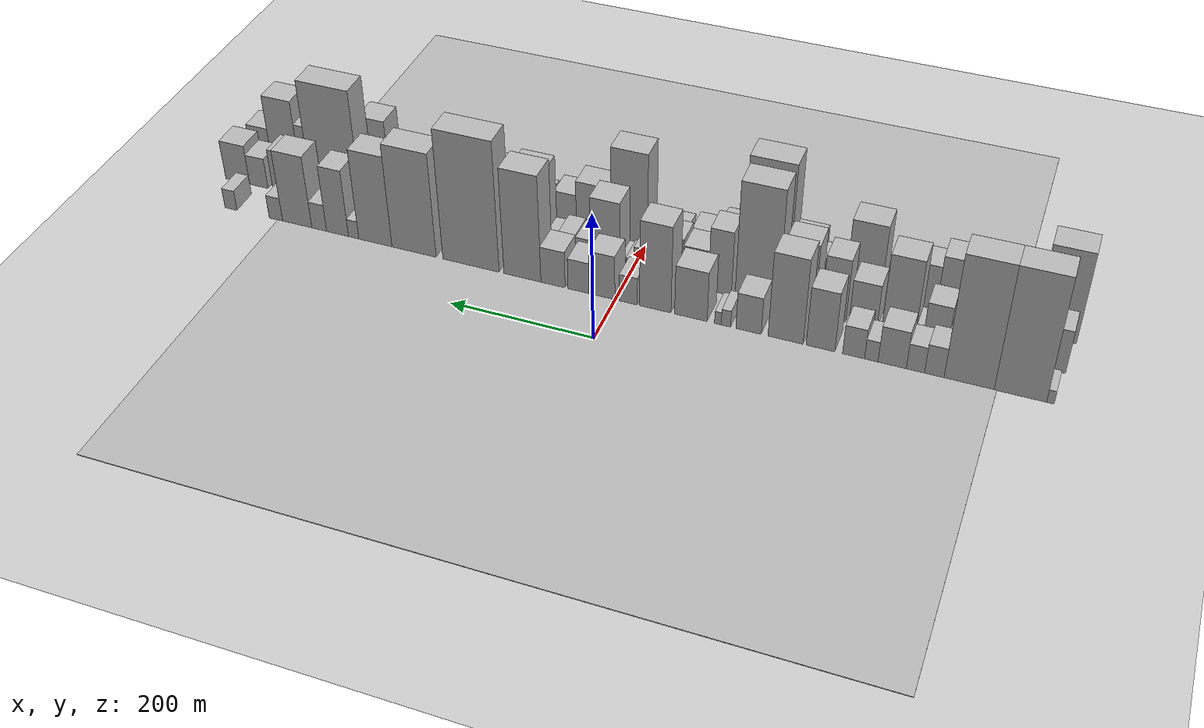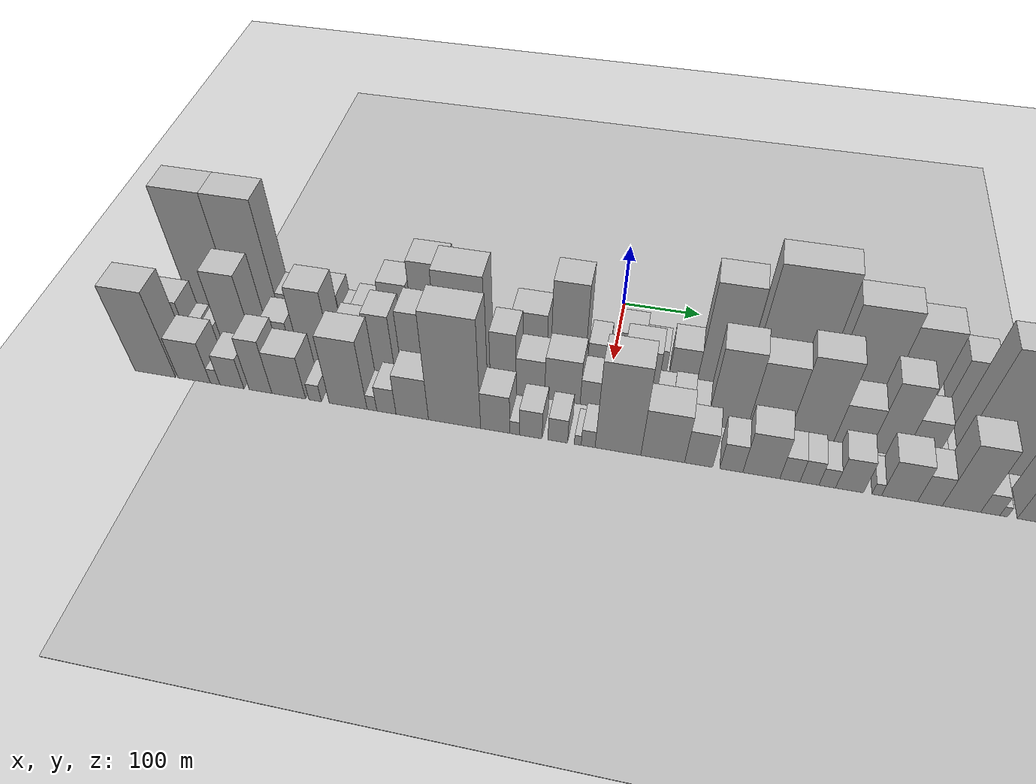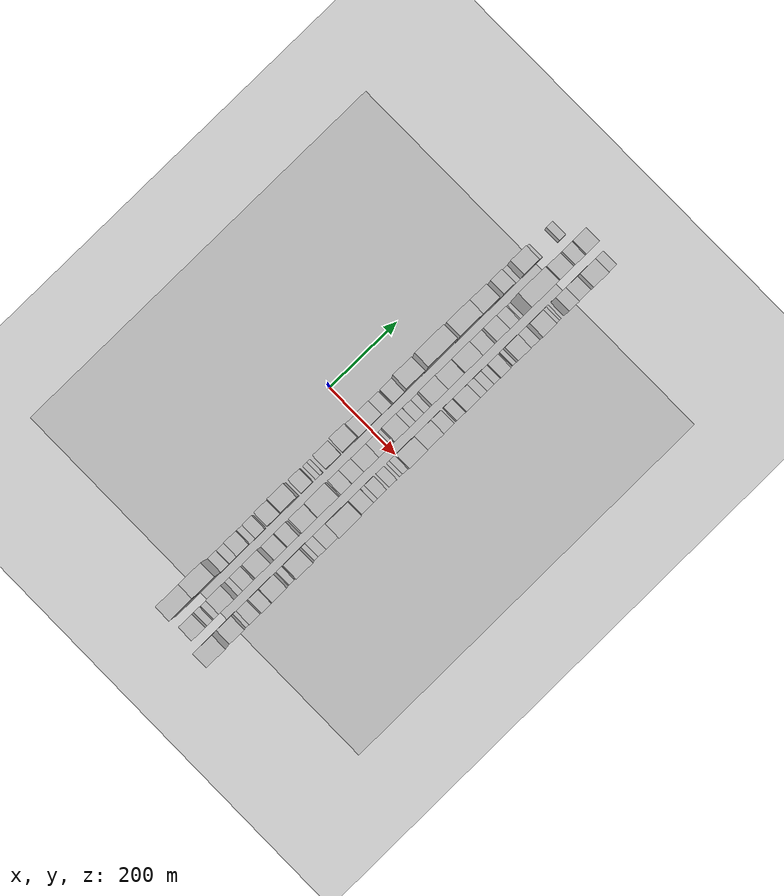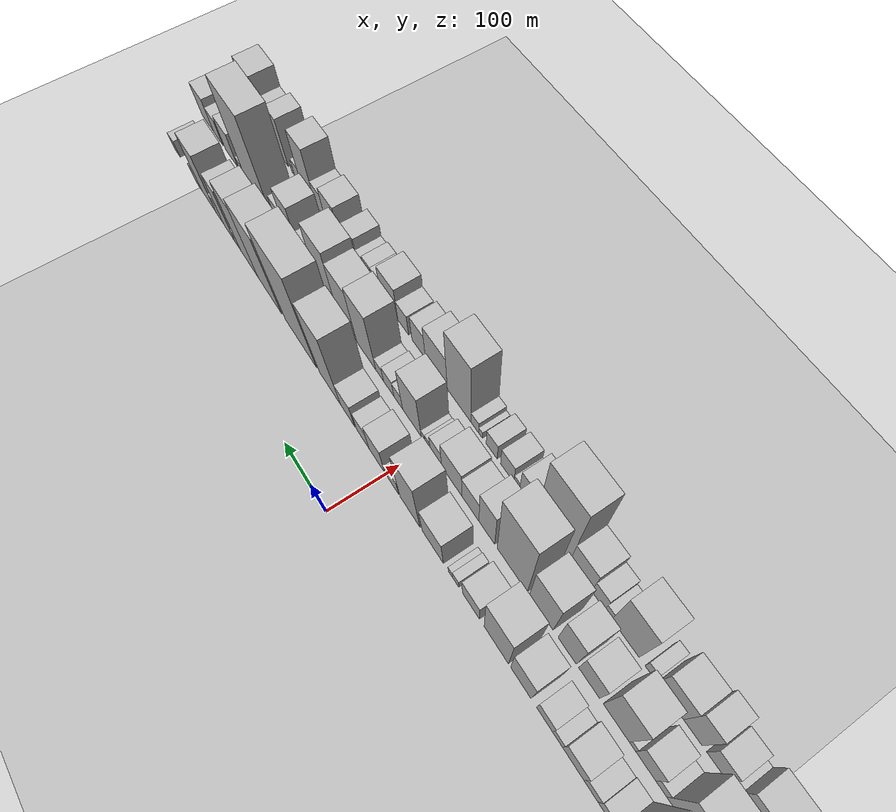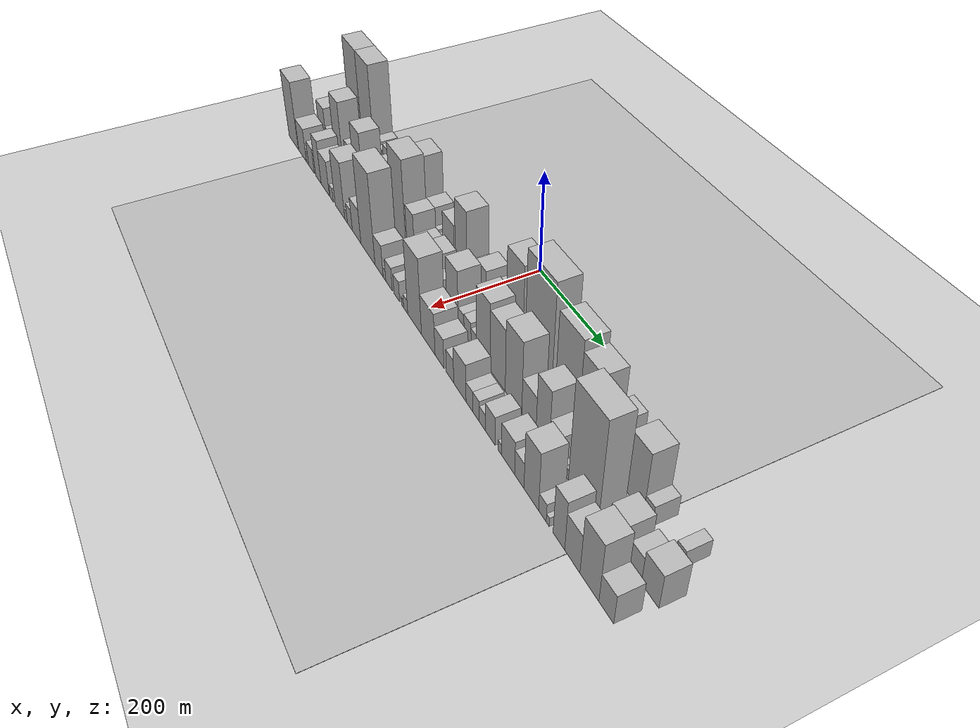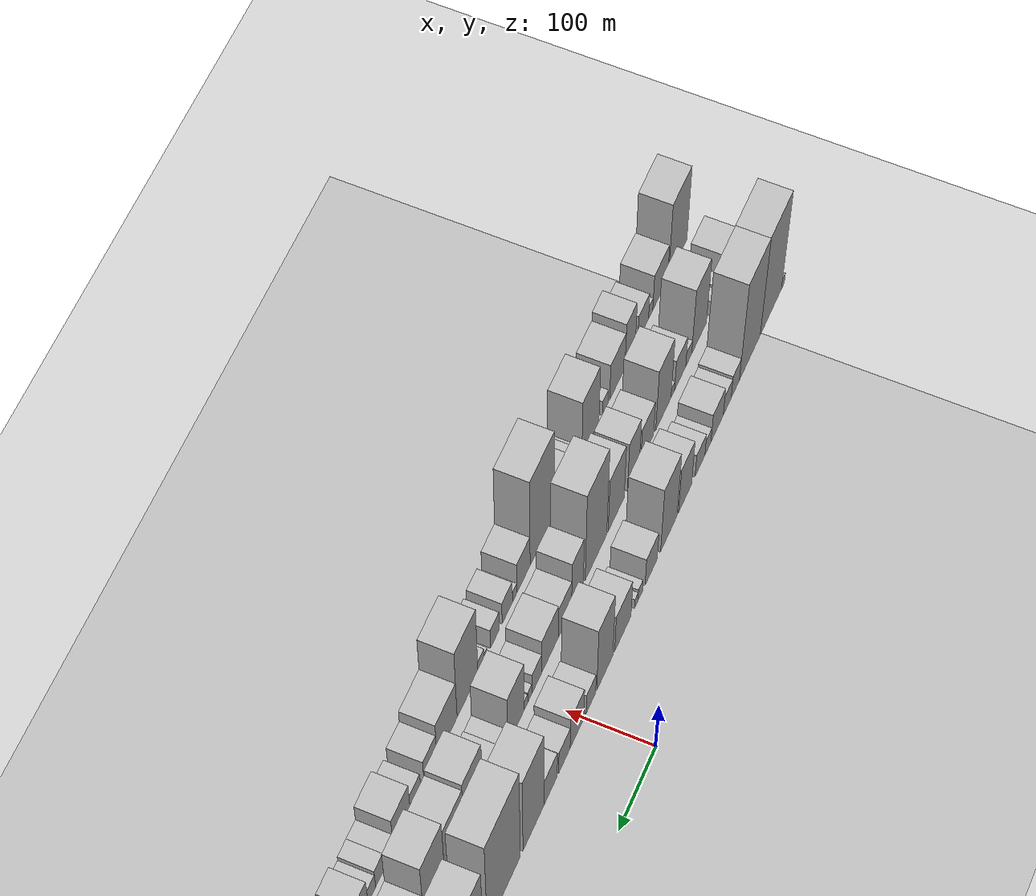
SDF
<?xml version="1.0" encoding="utf-8"?>

<sdf version="1.6">

   <world name="default">

      <gui fullscreen="0">

         <camera name="user_camera">

            <pose>-15 0 4.57585 0 0 0</pose>

            <view_controller>orbit</view_controller>

         </camera>

      </gui>

      <scene>

         <sky>

           <clouds>

             <speed>12</speed>

           </clouds>

         </sky>

         <ambient>0.4 0.4 0.4 1</ambient>

         <background>0.7 0.7 0.7 1</background>

         <shadows>1</shadows>

      </scene>

      <gravity>0 0 -9.8066</gravity>

      <magnetic_field>6e-06 2.3e-05 -4.2e-05</magnetic_field>

      <physics default="0" name="default_physics" type="ode">

         <ode>

            <solver>

               <type>quick</type>

               <iters>10</iters>

               <sor>1.0</sor>

               <use_dynamic_moi_rescaling>0</use_dynamic_moi_rescaling>

            </solver>

            <constraints>

               <cfm>0</cfm>

               <erp>0.2</erp>

               <contact_max_correcting_vel>100</contact_max_correcting_vel>

               <contact_surface_layer>0.001</contact_surface_layer>

            </constraints>

         </ode>

         <max_step_size>0.004</max_step_size>

         <real_time_factor>1</real_time_factor>

         <real_time_update_rate>250</real_time_update_rate>

      </physics>

      <light name="sun" type="directional">

         <cast_shadows>1</cast_shadows>

         <pose>0 0 10 0 0 0</pose>

         <diffuse>0.8 0.8 0.8 1</diffuse>

         <specular>0.2 0.2 0.2 1</specular>

         <attenuation>

            <range>1000</range>

            <constant>0.9</constant>

            <linear>0.01</linear>

            <quadratic>0.001</quadratic>

         </attenuation>

         <direction>-0.5 0.1 -0.9</direction>

      </light>

      <include>

         <name>ground_plane_1</name>

         <uri>model://HANNAS_ground_plane</uri>

         <pose>0 0 0  0 0 0</pose>

      </include>

      <include>

         <name>ground_plane_2</name>

         <uri>model://HANNAS_ground_plane</uri>

         <pose>100 0 0  0 0 0</pose>

      </include>

      <model name="building_1">

         <static>1</static>

         <pose frame="">100.0000 -565.3969 0 0.000000 0.000000 0.000000</pose>

         <link name="link">

            <pose frame="">0 0 10.50 0 0 0</pose>

            <collision name="collision">

               <geometry>

                  <box>

                     <size>40.0000 9.2063 21.0000</size>

                  </box>

               </geometry>

               <max_contacts>10</max_contacts>

               <surface>

                  <contact>

                     <ode/>

                  </contact>

                  <bounce/>

                  <friction>

                     <torsional>

                        <ode/>

                     </torsional>

                     <ode/>

                  </friction>

               </surface>

            </collision>

            <visual name="visual">

               <cast_shadows>0</cast_shadows>

               <geometry>

                  <box>

                     <size>40.0000 9.2063 21.0000</size>

                  </box>

               </geometry>

               <material>

                  <script>

                     <uri>model://HANNAS_wall/materials/scripts</uri>

                     <uri>model://HANNAS_wall/materials/textures</uri>

                     <name>vrc/HANNAS_wall</name>

                  </script>

               </material>

            </visual>

            <self_collide>0</self_collide>

            <enable_wind>0</enable_wind>

            <kinematic>0</kinematic>

         </link>

      </model>

      <model name="building_2">

         <static>1</static>

         <pose frame="">100.0000 -528.7531 0 0.000000 0.000000 0.000000</pose>

         <link name="link">

            <pose frame="">0 0 99.00 0 0 0</pose>

            <collision name="collision">

               <geometry>

                  <box>

                     <size>40.0000 64.0812 198.0000</size>

                  </box>

               </geometry>

               <max_contacts>10</max_contacts>

               <surface>

                  <contact>

                     <ode/>

                  </contact>

                  <bounce/>

                  <friction>

                     <torsional>

                        <ode/>

                     </torsional>

                     <ode/>

                  </friction>

               </surface>

            </collision>

            <visual name="visual">

               <cast_shadows>0</cast_shadows>

               <geometry>

                  <box>

                     <size>40.0000 64.0812 198.0000</size>

                  </box>

               </geometry>

               <material>

                  <script>

                     <uri>model://HANNAS_wall/materials/scripts</uri>

                     <uri>model://HANNAS_wall/materials/textures</uri>

                     <name>vrc/HANNAS_wall</name>

                  </script>

               </material>

            </visual>

            <self_collide>0</self_collide>

            <enable_wind>0</enable_wind>

            <kinematic>0</kinematic>

         </link>

      </model>

      <model name="building_3">

         <static>1</static>

         <pose frame="">100.0000 -465.5587 0 0.000000 0.000000 0.000000</pose>

         <link name="link">

            <pose frame="">0 0 99.00 0 0 0</pose>

            <collision name="collision">

               <geometry>

                  <box>

                     <size>40.0000 62.3076 198.0000</size>

                  </box>

               </geometry>

               <max_contacts>10</max_contacts>

               <surface>

                  <contact>

                     <ode/>

                  </contact>

                  <bounce/>

                  <friction>

                     <torsional>

                        <ode/>

                     </torsional>

                     <ode/>

                  </friction>

               </surface>

            </collision>

            <visual name="visual">

               <cast_shadows>0</cast_shadows>

               <geometry>

                  <box>

                     <size>40.0000 62.3076 198.0000</size>

                  </box>

               </geometry>

               <material>

                  <script>

                     <uri>model://HANNAS_wall/materials/scripts</uri>

                     <uri>model://HANNAS_wall/materials/textures</uri>

                     <name>vrc/HANNAS_wall</name>

                  </script>

               </material>

            </visual>

            <self_collide>0</self_collide>

            <enable_wind>0</enable_wind>

            <kinematic>0</kinematic>

         </link>

      </model>

      <model name="building_4">

         <static>1</static>

         <pose frame="">100.0000 -422.2081 0 0.000000 0.000000 0.000000</pose>

         <link name="link">

            <pose frame="">0 0 24.00 0 0 0</pose>

            <collision name="collision">

               <geometry>

                  <box>

                     <size>40.0000 24.3938 48.0000</size>

                  </box>

               </geometry>

               <max_contacts>10</max_contacts>

               <surface>

                  <contact>

                     <ode/>

                  </contact>

                  <bounce/>

                  <friction>

                     <torsional>

                        <ode/>

                     </torsional>

                     <ode/>

                  </friction>

               </surface>

            </collision>

            <visual name="visual">

               <cast_shadows>0</cast_shadows>

               <geometry>

                  <box>

                     <size>40.0000 24.3938 48.0000</size>

                  </box>

               </geometry>

               <material>

                  <script>

                     <uri>model://HANNAS_wall/materials/scripts</uri>

                     <uri>model://HANNAS_wall/materials/textures</uri>

                     <name>vrc/HANNAS_wall</name>

                  </script>

               </material>

            </visual>

            <self_collide>0</self_collide>

            <enable_wind>0</enable_wind>

            <kinematic>0</kinematic>

         </link>

      </model>

      <model name="building_5">

         <static>1</static>

         <pose frame="">100.0000 -398.4422 0 0.000000 0.000000 0.000000</pose>

         <link name="link">

            <pose frame="">0 0 21.00 0 0 0</pose>

            <collision name="collision">

               <geometry>

                  <box>

                     <size>40.0000 23.1380 42.0000</size>

                  </box>

               </geometry>

               <max_contacts>10</max_contacts>

               <surface>

                  <contact>

                     <ode/>

                  </contact>

                  <bounce/>

                  <friction>

                     <torsional>

                        <ode/>

                     </torsional>

                     <ode/>

                  </friction>

               </surface>

            </collision>

            <visual name="visual">

               <cast_shadows>0</cast_shadows>

               <geometry>

                  <box>

                     <size>40.0000 23.1380 42.0000</size>

                  </box>

               </geometry>

               <material>

                  <script>

                     <uri>model://HANNAS_wall/materials/scripts</uri>

                     <uri>model://HANNAS_wall/materials/textures</uri>

                     <name>vrc/HANNAS_wall</name>

                  </script>

               </material>

            </visual>

            <self_collide>0</self_collide>

            <enable_wind>0</enable_wind>

            <kinematic>0</kinematic>

         </link>

      </model>

      <model name="building_6">

         <static>1</static>

         <pose frame="">100.0000 -368.9011 0 0.000000 0.000000 0.000000</pose>

         <link name="link">

            <pose frame="">0 0 30.00 0 0 0</pose>

            <collision name="collision">

               <geometry>

                  <box>

                     <size>40.0000 35.9442 60.0000</size>

                  </box>

               </geometry>

               <max_contacts>10</max_contacts>

               <surface>

                  <contact>

                     <ode/>

                  </contact>

                  <bounce/>

                  <friction>

                     <torsional>

                        <ode/>

                     </torsional>

                     <ode/>

                  </friction>

               </surface>

            </collision>

            <visual name="visual">

               <cast_shadows>0</cast_shadows>

               <geometry>

                  <box>

                     <size>40.0000 35.9442 60.0000</size>

                  </box>

               </geometry>

               <material>

                  <script>

                     <uri>model://HANNAS_wall/materials/scripts</uri>

                     <uri>model://HANNAS_wall/materials/textures</uri>

                     <name>vrc/HANNAS_wall</name>

                  </script>

               </material>

            </visual>

            <self_collide>0</self_collide>

            <enable_wind>0</enable_wind>

            <kinematic>0</kinematic>

         </link>

      </model>

      <model name="building_7">

         <static>1</static>

         <pose frame="">100.0000 -342.2588 0 0.000000 0.000000 0.000000</pose>

         <link name="link">

            <pose frame="">0 0 16.50 0 0 0</pose>

            <collision name="collision">

               <geometry>

                  <box>

                     <size>40.0000 17.3405 33.0000</size>

                  </box>

               </geometry>

               <max_contacts>10</max_contacts>

               <surface>

                  <contact>

                     <ode/>

                  </contact>

                  <bounce/>

                  <friction>

                     <torsional>

                        <ode/>

                     </torsional>

                     <ode/>

                  </friction>

               </surface>

            </collision>

            <visual name="visual">

               <cast_shadows>0</cast_shadows>

               <geometry>

                  <box>

                     <size>40.0000 17.3405 33.0000</size>

                  </box>

               </geometry>

               <material>

                  <script>

                     <uri>model://HANNAS_wall/materials/scripts</uri>

                     <uri>model://HANNAS_wall/materials/textures</uri>

                     <name>vrc/HANNAS_wall</name>

                  </script>

               </material>

            </visual>

            <self_collide>0</self_collide>

            <enable_wind>0</enable_wind>

            <kinematic>0</kinematic>

         </link>

      </model>

      <model name="building_8">

         <static>1</static>

         <pose frame="">100.0000 -319.4504 0 0.000000 0.000000 0.000000</pose>

         <link name="link">

            <pose frame="">0 0 24.00 0 0 0</pose>

            <collision name="collision">

               <geometry>

                  <box>

                     <size>40.0000 28.2763 48.0000</size>

                  </box>

               </geometry>

               <max_contacts>10</max_contacts>

               <surface>

                  <contact>

                     <ode/>

                  </contact>

                  <bounce/>

                  <friction>

                     <torsional>

                        <ode/>

                     </torsional>

                     <ode/>

                  </friction>

               </surface>

            </collision>

            <visual name="visual">

               <cast_shadows>0</cast_shadows>

               <geometry>

                  <box>

                     <size>40.0000 28.2763 48.0000</size>

                  </box>

               </geometry>

               <material>

                  <script>

                     <uri>model://HANNAS_wall/materials/scripts</uri>

                     <uri>model://HANNAS_wall/materials/textures</uri>

                     <name>vrc/HANNAS_wall</name>

                  </script>

               </material>

            </visual>

            <self_collide>0</self_collide>

            <enable_wind>0</enable_wind>

            <kinematic>0</kinematic>

         </link>

      </model>

      <model name="building_9">

         <static>1</static>

         <pose frame="">100.0000 -276.6190 0 0.000000 0.000000 0.000000</pose>

         <link name="link">

            <pose frame="">0 0 48.00 0 0 0</pose>

            <collision name="collision">

               <geometry>

                  <box>

                     <size>40.0000 37.3865 96.0000</size>

                  </box>

               </geometry>

               <max_contacts>10</max_contacts>

               <surface>

                  <contact>

                     <ode/>

                  </contact>

                  <bounce/>

                  <friction>

                     <torsional>

                        <ode/>

                     </torsional>

                     <ode/>

                  </friction>

               </surface>

            </collision>

            <visual name="visual">

               <cast_shadows>0</cast_shadows>

               <geometry>

                  <box>

                     <size>40.0000 37.3865 96.0000</size>

                  </box>

               </geometry>

               <material>

                  <script>

                     <uri>model://HANNAS_wall/materials/scripts</uri>

                     <uri>model://HANNAS_wall/materials/textures</uri>

                     <name>vrc/HANNAS_wall</name>

                  </script>

               </material>

            </visual>

            <self_collide>0</self_collide>

            <enable_wind>0</enable_wind>

            <kinematic>0</kinematic>

         </link>

      </model>

      <model name="building_10">

         <static>1</static>

         <pose frame="">100.0000 -230.8028 0 0.000000 0.000000 0.000000</pose>

         <link name="link">

            <pose frame="">0 0 69.00 0 0 0</pose>

            <collision name="collision">

               <geometry>

                  <box>

                     <size>40.0000 46.2459 138.0000</size>

                  </box>

               </geometry>

               <max_contacts>10</max_contacts>

               <surface>

                  <contact>

                     <ode/>

                  </contact>

                  <bounce/>

                  <friction>

                     <torsional>

                        <ode/>

                     </torsional>

                     <ode/>

                  </friction>

               </surface>

            </collision>

            <visual name="visual">

               <cast_shadows>0</cast_shadows>

               <geometry>

                  <box>

                     <size>40.0000 46.2459 138.0000</size>

                  </box>

               </geometry>

               <material>

                  <script>

                     <uri>model://HANNAS_wall/materials/scripts</uri>

                     <uri>model://HANNAS_wall/materials/textures</uri>

                     <name>vrc/HANNAS_wall</name>

                  </script>

               </material>

            </visual>

            <self_collide>0</self_collide>

            <enable_wind>0</enable_wind>

            <kinematic>0</kinematic>

         </link>

      </model>

      <model name="building_11">

         <static>1</static>

         <pose frame="">100.0000 -181.7542 0 0.000000 0.000000 0.000000</pose>

         <link name="link">

            <pose frame="">0 0 30.00 0 0 0</pose>

            <collision name="collision">

               <geometry>

                  <box>

                     <size>40.0000 33.8512 60.0000</size>

                  </box>

               </geometry>

               <max_contacts>10</max_contacts>

               <surface>

                  <contact>

                     <ode/>

                  </contact>

                  <bounce/>

                  <friction>

                     <torsional>

                        <ode/>

                     </torsional>

                     <ode/>

                  </friction>

               </surface>

            </collision>

            <visual name="visual">

               <cast_shadows>0</cast_shadows>

               <geometry>

                  <box>

                     <size>40.0000 33.8512 60.0000</size>

                  </box>

               </geometry>

               <material>

                  <script>

                     <uri>model://HANNAS_wall/materials/scripts</uri>

                     <uri>model://HANNAS_wall/materials/textures</uri>

                     <name>vrc/HANNAS_wall</name>

                  </script>

               </material>

            </visual>

            <self_collide>0</self_collide>

            <enable_wind>0</enable_wind>

            <kinematic>0</kinematic>

         </link>

      </model>

      <model name="building_12">

         <static>1</static>

         <pose frame="">100.0000 -151.5063 0 0.000000 0.000000 0.000000</pose>

         <link name="link">

            <pose frame="">0 0 13.50 0 0 0</pose>

            <collision name="collision">

               <geometry>

                  <box>

                     <size>40.0000 12.6445 27.0000</size>

                  </box>

               </geometry>

               <max_contacts>10</max_contacts>

               <surface>

                  <contact>

                     <ode/>

                  </contact>

                  <bounce/>

                  <friction>

                     <torsional>

                        <ode/>

                     </torsional>

                     <ode/>

                  </friction>

               </surface>

            </collision>

            <visual name="visual">

               <cast_shadows>0</cast_shadows>

               <geometry>

                  <box>

                     <size>40.0000 12.6445 27.0000</size>

                  </box>

               </geometry>

               <material>

                  <script>

                     <uri>model://HANNAS_wall/materials/scripts</uri>

                     <uri>model://HANNAS_wall/materials/textures</uri>

                     <name>vrc/HANNAS_wall</name>

                  </script>

               </material>

            </visual>

            <self_collide>0</self_collide>

            <enable_wind>0</enable_wind>

            <kinematic>0</kinematic>

         </link>

      </model>

      <model name="building_13">

         <static>1</static>

         <pose frame="">100.0000 -140.6615 0 0.000000 0.000000 0.000000</pose>

         <link name="link">

            <pose frame="">0 0 10.50 0 0 0</pose>

            <collision name="collision">

               <geometry>

                  <box>

                     <size>40.0000 9.0451 21.0000</size>

                  </box>

               </geometry>

               <max_contacts>10</max_contacts>

               <surface>

                  <contact>

                     <ode/>

                  </contact>

                  <bounce/>

                  <friction>

                     <torsional>

                        <ode/>

                     </torsional>

                     <ode/>

                  </friction>

               </surface>

            </collision>

            <visual name="visual">

               <cast_shadows>0</cast_shadows>

               <geometry>

                  <box>

                     <size>40.0000 9.0451 21.0000</size>

                  </box>

               </geometry>

               <material>

                  <script>

                     <uri>model://HANNAS_wall/materials/scripts</uri>

                     <uri>model://HANNAS_wall/materials/textures</uri>

                     <name>vrc/HANNAS_wall</name>

                  </script>

               </material>

            </visual>

            <self_collide>0</self_collide>

            <enable_wind>0</enable_wind>

            <kinematic>0</kinematic>

         </link>

      </model>

      <model name="building_14">

         <static>1</static>

         <pose frame="">100.0000 -103.9744 0 0.000000 0.000000 0.000000</pose>

         <link name="link">

            <pose frame="">0 0 40.50 0 0 0</pose>

            <collision name="collision">

               <geometry>

                  <box>

                     <size>40.0000 44.3291 81.0000</size>

                  </box>

               </geometry>

               <max_contacts>10</max_contacts>

               <surface>

                  <contact>

                     <ode/>

                  </contact>

                  <bounce/>

                  <friction>

                     <torsional>

                        <ode/>

                     </torsional>

                     <ode/>

                  </friction>

               </surface>

            </collision>

            <visual name="visual">

               <cast_shadows>0</cast_shadows>

               <geometry>

                  <box>

                     <size>40.0000 44.3291 81.0000</size>

                  </box>

               </geometry>

               <material>

                  <script>

                     <uri>model://HANNAS_wall/materials/scripts</uri>

                     <uri>model://HANNAS_wall/materials/textures</uri>

                     <name>vrc/HANNAS_wall</name>

                  </script>

               </material>

            </visual>

            <self_collide>0</self_collide>

            <enable_wind>0</enable_wind>

            <kinematic>0</kinematic>

         </link>

      </model>

      <model name="building_15">

         <static>1</static>

         <pose frame="">100.0000 -55.1464 0 0.000000 0.000000 0.000000</pose>

         <link name="link">

            <pose frame="">0 0 70.50 0 0 0</pose>

            <collision name="collision">

               <geometry>

                  <box>

                     <size>40.0000 43.3270 141.0000</size>

                  </box>

               </geometry>

               <max_contacts>10</max_contacts>

               <surface>

                  <contact>

                     <ode/>

                  </contact>

                  <bounce/>

                  <friction>

                     <torsional>

                        <ode/>

                     </torsional>

                     <ode/>

                  </friction>

               </surface>

            </collision>

            <visual name="visual">

               <cast_shadows>0</cast_shadows>

               <geometry>

                  <box>

                     <size>40.0000 43.3270 141.0000</size>

                  </box>

               </geometry>

               <material>

                  <script>

                     <uri>model://HANNAS_wall/materials/scripts</uri>

                     <uri>model://HANNAS_wall/materials/textures</uri>

                     <name>vrc/HANNAS_wall</name>

                  </script>

               </material>

            </visual>

            <self_collide>0</self_collide>

            <enable_wind>0</enable_wind>

            <kinematic>0</kinematic>

         </link>

      </model>

      <model name="building_16">

         <static>1</static>

         <pose frame="">100.0000 -17.9122 0 0.000000 0.000000 0.000000</pose>

         <link name="link">

            <pose frame="">0 0 22.50 0 0 0</pose>

            <collision name="collision">

               <geometry>

                  <box>

                     <size>40.0000 25.1414 45.0000</size>

                  </box>

               </geometry>

               <max_contacts>10</max_contacts>

               <surface>

                  <contact>

                     <ode/>

                  </contact>

                  <bounce/>

                  <friction>

                     <torsional>

                        <ode/>

                     </torsional>

                     <ode/>

                  </friction>

               </surface>

            </collision>

            <visual name="visual">

               <cast_shadows>0</cast_shadows>

               <geometry>

                  <box>

                     <size>40.0000 25.1414 45.0000</size>

                  </box>

               </geometry>

               <material>

                  <script>

                     <uri>model://HANNAS_wall/materials/scripts</uri>

                     <uri>model://HANNAS_wall/materials/textures</uri>

                     <name>vrc/HANNAS_wall</name>

                  </script>

               </material>

            </visual>

            <self_collide>0</self_collide>

            <enable_wind>0</enable_wind>

            <kinematic>0</kinematic>

         </link>

      </model>

      <model name="building_17">

         <static>1</static>

         <pose frame="">100.0000 18.7852 0 0.000000 0.000000 0.000000</pose>

         <link name="link">

            <pose frame="">0 0 36.00 0 0 0</pose>

            <collision name="collision">

               <geometry>

                  <box>

                     <size>40.0000 36.2534 72.0000</size>

                  </box>

               </geometry>

               <max_contacts>10</max_contacts>

               <surface>

                  <contact>

                     <ode/>

                  </contact>

                  <bounce/>

                  <friction>

                     <torsional>

                        <ode/>

                     </torsional>

                     <ode/>

                  </friction>

               </surface>

            </collision>

            <visual name="visual">

               <cast_shadows>0</cast_shadows>

               <geometry>

                  <box>

                     <size>40.0000 36.2534 72.0000</size>

                  </box>

               </geometry>

               <material>

                  <script>

                     <uri>model://HANNAS_wall/materials/scripts</uri>

                     <uri>model://HANNAS_wall/materials/textures</uri>

                     <name>vrc/HANNAS_wall</name>

                  </script>

               </material>

            </visual>

            <self_collide>0</self_collide>

            <enable_wind>0</enable_wind>

            <kinematic>0</kinematic>

         </link>

      </model>

      <model name="building_18">

         <static>1</static>

         <pose frame="">100.0000 51.7863 0 0.000000 0.000000 0.000000</pose>

         <link name="link">

            <pose frame="">0 0 25.50 0 0 0</pose>

            <collision name="collision">

               <geometry>

                  <box>

                     <size>40.0000 29.7487 51.0000</size>

                  </box>

               </geometry>

               <max_contacts>10</max_contacts>

               <surface>

                  <contact>

                     <ode/>

                  </contact>

                  <bounce/>

                  <friction>

                     <torsional>

                        <ode/>

                     </torsional>

                     <ode/>

                  </friction>

               </surface>

            </collision>

            <visual name="visual">

               <cast_shadows>0</cast_shadows>

               <geometry>

                  <box>

                     <size>40.0000 29.7487 51.0000</size>

                  </box>

               </geometry>

               <material>

                  <script>

                     <uri>model://HANNAS_wall/materials/scripts</uri>

                     <uri>model://HANNAS_wall/materials/textures</uri>

                     <name>vrc/HANNAS_wall</name>

                  </script>

               </material>

            </visual>

            <self_collide>0</self_collide>

            <enable_wind>0</enable_wind>

            <kinematic>0</kinematic>

         </link>

      </model>

      <model name="building_19">

         <static>1</static>

         <pose frame="">100.0000 87.9456 0 0.000000 0.000000 0.000000</pose>

         <link name="link">

            <pose frame="">0 0 30.00 0 0 0</pose>

            <collision name="collision">

               <geometry>

                  <box>

                     <size>40.0000 34.5700 60.0000</size>

                  </box>

               </geometry>

               <max_contacts>10</max_contacts>

               <surface>

                  <contact>

                     <ode/>

                  </contact>

                  <bounce/>

                  <friction>

                     <torsional>

                        <ode/>

                     </torsional>

                     <ode/>

                  </friction>

               </surface>

            </collision>

            <visual name="visual">

               <cast_shadows>0</cast_shadows>

               <geometry>

                  <box>

                     <size>40.0000 34.5700 60.0000</size>

                  </box>

               </geometry>

               <material>

                  <script>

                     <uri>model://HANNAS_wall/materials/scripts</uri>

                     <uri>model://HANNAS_wall/materials/textures</uri>

                     <name>vrc/HANNAS_wall</name>

                  </script>

               </material>

            </visual>

            <self_collide>0</self_collide>

            <enable_wind>0</enable_wind>

            <kinematic>0</kinematic>

         </link>

      </model>

      <model name="building_20">

         <static>1</static>

         <pose frame="">100.0000 131.8592 0 0.000000 0.000000 0.000000</pose>

         <link name="link">

            <pose frame="">0 0 87.00 0 0 0</pose>

            <collision name="collision">

               <geometry>

                  <box>

                     <size>40.0000 53.2572 174.0000</size>

                  </box>

               </geometry>

               <max_contacts>10</max_contacts>

               <surface>

                  <contact>

                     <ode/>

                  </contact>

                  <bounce/>

                  <friction>

                     <torsional>

                        <ode/>

                     </torsional>

                     <ode/>

                  </friction>

               </surface>

            </collision>

            <visual name="visual">

               <cast_shadows>0</cast_shadows>

               <geometry>

                  <box>

                     <size>40.0000 53.2572 174.0000</size>

                  </box>

               </geometry>

               <material>

                  <script>

                     <uri>model://HANNAS_wall/materials/scripts</uri>

                     <uri>model://HANNAS_wall/materials/textures</uri>

                     <name>vrc/HANNAS_wall</name>

                  </script>

               </material>

            </visual>

            <self_collide>0</self_collide>

            <enable_wind>0</enable_wind>

            <kinematic>0</kinematic>

         </link>

      </model>

      <model name="building_21">

         <static>1</static>

         <pose frame="">100.0000 206.7829 0 0.000000 0.000000 0.000000</pose>

         <link name="link">

            <pose frame="">0 0 106.50 0 0 0</pose>

            <collision name="collision">

               <geometry>

                  <box>

                     <size>40.0000 82.5902 213.0000</size>

                  </box>

               </geometry>

               <max_contacts>10</max_contacts>

               <surface>

                  <contact>

                     <ode/>

                  </contact>

                  <bounce/>

                  <friction>

                     <torsional>

                        <ode/>

                     </torsional>

                     <ode/>

                  </friction>

               </surface>

            </collision>

            <visual name="visual">

               <cast_shadows>0</cast_shadows>

               <geometry>

                  <box>

                     <size>40.0000 82.5902 213.0000</size>

                  </box>

               </geometry>

               <material>

                  <script>

                     <uri>model://HANNAS_wall/materials/scripts</uri>

                     <uri>model://HANNAS_wall/materials/textures</uri>

                     <name>vrc/HANNAS_wall</name>

                  </script>

               </material>

            </visual>

            <self_collide>0</self_collide>

            <enable_wind>0</enable_wind>

            <kinematic>0</kinematic>

         </link>

      </model>

      <model name="building_22">

         <static>1</static>

         <pose frame="">100.0000 291.1268 0 0.000000 0.000000 0.000000</pose>

         <link name="link">

            <pose frame="">0 0 85.50 0 0 0</pose>

            <collision name="collision">

               <geometry>

                  <box>

                     <size>40.0000 66.0975 171.0000</size>

                  </box>

               </geometry>

               <max_contacts>10</max_contacts>

               <surface>

                  <contact>

                     <ode/>

                  </contact>

                  <bounce/>

                  <friction>

                     <torsional>

                        <ode/>

                     </torsional>

                     <ode/>

                  </friction>

               </surface>

            </collision>

            <visual name="visual">

               <cast_shadows>0</cast_shadows>

               <geometry>

                  <box>

                     <size>40.0000 66.0975 171.0000</size>

                  </box>

               </geometry>

               <material>

                  <script>

                     <uri>model://HANNAS_wall/materials/scripts</uri>

                     <uri>model://HANNAS_wall/materials/textures</uri>

                     <name>vrc/HANNAS_wall</name>

                  </script>

               </material>

            </visual>

            <self_collide>0</self_collide>

            <enable_wind>0</enable_wind>

            <kinematic>0</kinematic>

         </link>

      </model>

      <model name="building_23">

         <static>1</static>

         <pose frame="">100.0000 349.3756 0 0.000000 0.000000 0.000000</pose>

         <link name="link">

            <pose frame="">0 0 75.00 0 0 0</pose>

            <collision name="collision">

               <geometry>

                  <box>

                     <size>40.0000 50.4002 150.0000</size>

                  </box>

               </geometry>

               <max_contacts>10</max_contacts>

               <surface>

                  <contact>

                     <ode/>

                  </contact>

                  <bounce/>

                  <friction>

                     <torsional>

                        <ode/>

                     </torsional>

                     <ode/>

                  </friction>

               </surface>

            </collision>

            <visual name="visual">

               <cast_shadows>0</cast_shadows>

               <geometry>

                  <box>

                     <size>40.0000 50.4002 150.0000</size>

                  </box>

               </geometry>

               <material>

                  <script>

                     <uri>model://HANNAS_wall/materials/scripts</uri>

                     <uri>model://HANNAS_wall/materials/textures</uri>

                     <name>vrc/HANNAS_wall</name>

                  </script>

               </material>

            </visual>

            <self_collide>0</self_collide>

            <enable_wind>0</enable_wind>

            <kinematic>0</kinematic>

         </link>

      </model>

      <model name="building_24">

         <static>1</static>

         <pose frame="">100.0000 382.4126 0 0.000000 0.000000 0.000000</pose>

         <link name="link">

            <pose frame="">0 0 15.00 0 0 0</pose>

            <collision name="collision">

               <geometry>

                  <box>

                     <size>40.0000 15.6738 30.0000</size>

                  </box>

               </geometry>

               <max_contacts>10</max_contacts>

               <surface>

                  <contact>

                     <ode/>

                  </contact>

                  <bounce/>

                  <friction>

                     <torsional>

                        <ode/>

                     </torsional>

                     <ode/>

                  </friction>

               </surface>

            </collision>

            <visual name="visual">

               <cast_shadows>0</cast_shadows>

               <geometry>

                  <box>

                     <size>40.0000 15.6738 30.0000</size>

                  </box>

               </geometry>

               <material>

                  <script>

                     <uri>model://HANNAS_wall/materials/scripts</uri>

                     <uri>model://HANNAS_wall/materials/textures</uri>

                     <name>vrc/HANNAS_wall</name>

                  </script>

               </material>

            </visual>

            <self_collide>0</self_collide>

            <enable_wind>0</enable_wind>

            <kinematic>0</kinematic>

         </link>

      </model>

      <model name="building_25">

         <static>1</static>

         <pose frame="">100.0000 407.1039 0 0.000000 0.000000 0.000000</pose>

         <link name="link">

            <pose frame="">0 0 55.50 0 0 0</pose>

            <collision name="collision">

               <geometry>

                  <box>

                     <size>40.0000 33.7089 111.0000</size>

                  </box>

               </geometry>

               <max_contacts>10</max_contacts>

               <surface>

                  <contact>

                     <ode/>

                  </contact>

                  <bounce/>

                  <friction>

                     <torsional>

                        <ode/>

                     </torsional>

                     <ode/>

                  </friction>

               </surface>

            </collision>

            <visual name="visual">

               <cast_shadows>0</cast_shadows>

               <geometry>

                  <box>

                     <size>40.0000 33.7089 111.0000</size>

                  </box>

               </geometry>

               <material>

                  <script>

                     <uri>model://HANNAS_wall/materials/scripts</uri>

                     <uri>model://HANNAS_wall/materials/textures</uri>

                     <name>vrc/HANNAS_wall</name>

                  </script>

               </material>

            </visual>

            <self_collide>0</self_collide>

            <enable_wind>0</enable_wind>

            <kinematic>0</kinematic>

         </link>

      </model>

      <model name="building_26">

         <static>1</static>

         <pose frame="">100.0000 435.3953 0 0.000000 0.000000 0.000000</pose>

         <link name="link">

            <pose frame="">0 0 22.50 0 0 0</pose>

            <collision name="collision">

               <geometry>

                  <box>

                     <size>40.0000 22.8740 45.0000</size>

                  </box>

               </geometry>

               <max_contacts>10</max_contacts>

               <surface>

                  <contact>

                     <ode/>

                  </contact>

                  <bounce/>

                  <friction>

                     <torsional>

                        <ode/>

                     </torsional>

                     <ode/>

                  </friction>

               </surface>

            </collision>

            <visual name="visual">

               <cast_shadows>0</cast_shadows>

               <geometry>

                  <box>

                     <size>40.0000 22.8740 45.0000</size>

                  </box>

               </geometry>

               <material>

                  <script>

                     <uri>model://HANNAS_wall/materials/scripts</uri>

                     <uri>model://HANNAS_wall/materials/textures</uri>

                     <name>vrc/HANNAS_wall</name>

                  </script>

               </material>

            </visual>

            <self_collide>0</self_collide>

            <enable_wind>0</enable_wind>

            <kinematic>0</kinematic>

         </link>

      </model>

      <model name="building_27">

         <static>1</static>

         <pose frame="">100.0000 469.7228 0 0.000000 0.000000 0.000000</pose>

         <link name="link">

            <pose frame="">0 0 60.00 0 0 0</pose>

            <collision name="collision">

               <geometry>

                  <box>

                     <size>40.0000 45.7809 120.0000</size>

                  </box>

               </geometry>

               <max_contacts>10</max_contacts>

               <surface>

                  <contact>

                     <ode/>

                  </contact>

                  <bounce/>

                  <friction>

                     <torsional>

                        <ode/>

                     </torsional>

                     <ode/>

                  </friction>

               </surface>

            </collision>

            <visual name="visual">

               <cast_shadows>0</cast_shadows>

               <geometry>

                  <box>

                     <size>40.0000 45.7809 120.0000</size>

                  </box>

               </geometry>

               <material>

                  <script>

                     <uri>model://HANNAS_wall/materials/scripts</uri>

                     <uri>model://HANNAS_wall/materials/textures</uri>

                     <name>vrc/HANNAS_wall</name>

                  </script>

               </material>

            </visual>

            <self_collide>0</self_collide>

            <enable_wind>0</enable_wind>

            <kinematic>0</kinematic>

         </link>

      </model>

      <model name="building_28">

         <static>1</static>

         <pose frame="">100.0000 503.0338 0 0.000000 0.000000 0.000000</pose>

         <link name="link">

            <pose frame="">0 0 19.50 0 0 0</pose>

            <collision name="collision">

               <geometry>

                  <box>

                     <size>40.0000 20.8411 39.0000</size>

                  </box>

               </geometry>

               <max_contacts>10</max_contacts>

               <surface>

                  <contact>

                     <ode/>

                  </contact>

                  <bounce/>

                  <friction>

                     <torsional>

                        <ode/>

                     </torsional>

                     <ode/>

                  </friction>

               </surface>

            </collision>

            <visual name="visual">

               <cast_shadows>0</cast_shadows>

               <geometry>

                  <box>

                     <size>40.0000 20.8411 39.0000</size>

                  </box>

               </geometry>

               <material>

                  <script>

                     <uri>model://HANNAS_wall/materials/scripts</uri>

                     <uri>model://HANNAS_wall/materials/textures</uri>

                     <name>vrc/HANNAS_wall</name>

                  </script>

               </material>

            </visual>

            <self_collide>0</self_collide>

            <enable_wind>0</enable_wind>

            <kinematic>0</kinematic>

         </link>

      </model>

      <model name="building_29">

         <static>1</static>

         <pose frame="">100.0000 574.2659 0 0.000000 0.000000 0.000000</pose>

         <link name="link">

            <pose frame="">0 0 16.50 0 0 0</pose>

            <collision name="collision">

               <geometry>

                  <box>

                     <size>40.0000 19.2077 33.0000</size>

                  </box>

               </geometry>

               <max_contacts>10</max_contacts>

               <surface>

                  <contact>

                     <ode/>

                  </contact>

                  <bounce/>

                  <friction>

                     <torsional>

                        <ode/>

                     </torsional>

                     <ode/>

                  </friction>

               </surface>

            </collision>

            <visual name="visual">

               <cast_shadows>0</cast_shadows>

               <geometry>

                  <box>

                     <size>40.0000 19.2077 33.0000</size>

                  </box>

               </geometry>

               <material>

                  <script>

                     <uri>model://HANNAS_wall/materials/scripts</uri>

                     <uri>model://HANNAS_wall/materials/textures</uri>

                     <name>vrc/HANNAS_wall</name>

                  </script>

               </material>

            </visual>

            <self_collide>0</self_collide>

            <enable_wind>0</enable_wind>

            <kinematic>0</kinematic>

         </link>

      </model>

      <model name="building_30">

         <static>1</static>

         <pose frame="">160.0000 -555.3085 0 0.000000 0.000000 0.000000</pose>

         <link name="link">

            <pose frame="">0 0 34.50 0 0 0</pose>

            <collision name="collision">

               <geometry>

                  <box>

                     <size>40.0000 39.3831 69.0000</size>

                  </box>

               </geometry>

               <max_contacts>10</max_contacts>

               <surface>

                  <contact>

                     <ode/>

                  </contact>

                  <bounce/>

                  <friction>

                     <torsional>

                        <ode/>

                     </torsional>

                     <ode/>

                  </friction>

               </surface>

            </collision>

            <visual name="visual">

               <cast_shadows>0</cast_shadows>

               <geometry>

                  <box>

                     <size>40.0000 39.3831 69.0000</size>

                  </box>

               </geometry>

               <material>

                  <script>

                     <uri>model://HANNAS_wall/materials/scripts</uri>

                     <uri>model://HANNAS_wall/materials/textures</uri>

                     <name>vrc/HANNAS_wall</name>

                  </script>

               </material>

            </visual>

            <self_collide>0</self_collide>

            <enable_wind>0</enable_wind>

            <kinematic>0</kinematic>

         </link>

      </model>

      <model name="building_31">

         <static>1</static>

         <pose frame="">160.0000 -527.1976 0 0.000000 0.000000 0.000000</pose>

         <link name="link">

            <pose frame="">0 0 15.00 0 0 0</pose>

            <collision name="collision">

               <geometry>

                  <box>

                     <size>40.0000 16.8386 30.0000</size>

                  </box>

               </geometry>

               <max_contacts>10</max_contacts>

               <surface>

                  <contact>

                     <ode/>

                  </contact>

                  <bounce/>

                  <friction>

                     <torsional>

                        <ode/>

                     </torsional>

                     <ode/>

                  </friction>

               </surface>

            </collision>

            <visual name="visual">

               <cast_shadows>0</cast_shadows>

               <geometry>

                  <box>

                     <size>40.0000 16.8386 30.0000</size>

                  </box>

               </geometry>

               <material>

                  <script>

                     <uri>model://HANNAS_wall/materials/scripts</uri>

                     <uri>model://HANNAS_wall/materials/textures</uri>

                     <name>vrc/HANNAS_wall</name>

                  </script>

               </material>

            </visual>

            <self_collide>0</self_collide>

            <enable_wind>0</enable_wind>

            <kinematic>0</kinematic>

         </link>

      </model>

      <model name="building_32">

         <static>1</static>

         <pose frame="">160.0000 -507.0286 0 0.000000 0.000000 0.000000</pose>

         <link name="link">

            <pose frame="">0 0 15.00 0 0 0</pose>

            <collision name="collision">

               <geometry>

                  <box>

                     <size>40.0000 17.4994 30.0000</size>

                  </box>

               </geometry>

               <max_contacts>10</max_contacts>

               <surface>

                  <contact>

                     <ode/>

                  </contact>

                  <bounce/>

                  <friction>

                     <torsional>

                        <ode/>

                     </torsional>

                     <ode/>

                  </friction>

               </surface>

            </collision>

            <visual name="visual">

               <cast_shadows>0</cast_shadows>

               <geometry>

                  <box>

                     <size>40.0000 17.4994 30.0000</size>

                  </box>

               </geometry>

               <material>

                  <script>

                     <uri>model://HANNAS_wall/materials/scripts</uri>

                     <uri>model://HANNAS_wall/materials/textures</uri>

                     <name>vrc/HANNAS_wall</name>

                  </script>

               </material>

            </visual>

            <self_collide>0</self_collide>

            <enable_wind>0</enable_wind>

            <kinematic>0</kinematic>

         </link>

      </model>

      <model name="building_33">

         <static>1</static>

         <pose frame="">160.0000 -466.6407 0 0.000000 0.000000 0.000000</pose>

         <link name="link">

            <pose frame="">0 0 66.00 0 0 0</pose>

            <collision name="collision">

               <geometry>

                  <box>

                     <size>40.0000 43.2764 132.0000</size>

                  </box>

               </geometry>

               <max_contacts>10</max_contacts>

               <surface>

                  <contact>

                     <ode/>

                  </contact>

                  <bounce/>

                  <friction>

                     <torsional>

                        <ode/>

                     </torsional>

                     <ode/>

                  </friction>

               </surface>

            </collision>

            <visual name="visual">

               <cast_shadows>0</cast_shadows>

               <geometry>

                  <box>

                     <size>40.0000 43.2764 132.0000</size>

                  </box>

               </geometry>

               <material>

                  <script>

                     <uri>model://HANNAS_wall/materials/scripts</uri>

                     <uri>model://HANNAS_wall/materials/textures</uri>

                     <name>vrc/HANNAS_wall</name>

                  </script>

               </material>

            </visual>

            <self_collide>0</self_collide>

            <enable_wind>0</enable_wind>

            <kinematic>0</kinematic>

         </link>

      </model>

      <model name="building_34">

         <static>1</static>

         <pose frame="">160.0000 -436.3407 0 0.000000 0.000000 0.000000</pose>

         <link name="link">

            <pose frame="">0 0 15.00 0 0 0</pose>

            <collision name="collision">

               <geometry>

                  <box>

                     <size>40.0000 17.3237 30.0000</size>

                  </box>

               </geometry>

               <max_contacts>10</max_contacts>

               <surface>

                  <contact>

                     <ode/>

                  </contact>

                  <bounce/>

                  <friction>

                     <torsional>

                        <ode/>

                     </torsional>

                     <ode/>

                  </friction>

               </surface>

            </collision>

            <visual name="visual">

               <cast_shadows>0</cast_shadows>

               <geometry>

                  <box>

                     <size>40.0000 17.3237 30.0000</size>

                  </box>

               </geometry>

               <material>

                  <script>

                     <uri>model://HANNAS_wall/materials/scripts</uri>

                     <uri>model://HANNAS_wall/materials/textures</uri>

                     <name>vrc/HANNAS_wall</name>

                  </script>

               </material>

            </visual>

            <self_collide>0</self_collide>

            <enable_wind>0</enable_wind>

            <kinematic>0</kinematic>

         </link>

      </model>

      <model name="building_35">

         <static>1</static>

         <pose frame="">160.0000 -411.4099 0 0.000000 0.000000 0.000000</pose>

         <link name="link">

            <pose frame="">0 0 31.50 0 0 0</pose>

            <collision name="collision">

               <geometry>

                  <box>

                     <size>40.0000 32.5379 63.0000</size>

                  </box>

               </geometry>

               <max_contacts>10</max_contacts>

               <surface>

                  <contact>

                     <ode/>

                  </contact>

                  <bounce/>

                  <friction>

                     <torsional>

                        <ode/>

                     </torsional>

                     <ode/>

                  </friction>

               </surface>

            </collision>

            <visual name="visual">

               <cast_shadows>0</cast_shadows>

               <geometry>

                  <box>

                     <size>40.0000 32.5379 63.0000</size>

                  </box>

               </geometry>

               <material>

                  <script>

                     <uri>model://HANNAS_wall/materials/scripts</uri>

                     <uri>model://HANNAS_wall/materials/textures</uri>

                     <name>vrc/HANNAS_wall</name>

                  </script>

               </material>

            </visual>

            <self_collide>0</self_collide>

            <enable_wind>0</enable_wind>

            <kinematic>0</kinematic>

         </link>

      </model>

      <model name="building_36">

         <static>1</static>

         <pose frame="">160.0000 -390.1044 0 0.000000 0.000000 0.000000</pose>

         <link name="link">

            <pose frame="">0 0 10.50 0 0 0</pose>

            <collision name="collision">

               <geometry>

                  <box>

                     <size>40.0000 10.0730 21.0000</size>

                  </box>

               </geometry>

               <max_contacts>10</max_contacts>

               <surface>

                  <contact>

                     <ode/>

                  </contact>

                  <bounce/>

                  <friction>

                     <torsional>

                        <ode/>

                     </torsional>

                     <ode/>

                  </friction>

               </surface>

            </collision>

            <visual name="visual">

               <cast_shadows>0</cast_shadows>

               <geometry>

                  <box>

                     <size>40.0000 10.0730 21.0000</size>

                  </box>

               </geometry>

               <material>

                  <script>

                     <uri>model://HANNAS_wall/materials/scripts</uri>

                     <uri>model://HANNAS_wall/materials/textures</uri>

                     <name>vrc/HANNAS_wall</name>

                  </script>

               </material>

            </visual>

            <self_collide>0</self_collide>

            <enable_wind>0</enable_wind>

            <kinematic>0</kinematic>

         </link>

      </model>

      <model name="building_37">

         <static>1</static>

         <pose frame="">160.0000 -363.1750 0 0.000000 0.000000 0.000000</pose>

         <link name="link">

            <pose frame="">0 0 63.00 0 0 0</pose>

            <collision name="collision">

               <geometry>

                  <box>

                     <size>40.0000 43.7858 126.0000</size>

                  </box>

               </geometry>

               <max_contacts>10</max_contacts>

               <surface>

                  <contact>

                     <ode/>

                  </contact>

                  <bounce/>

                  <friction>

                     <torsional>

                        <ode/>

                     </torsional>

                     <ode/>

                  </friction>

               </surface>

            </collision>

            <visual name="visual">

               <cast_shadows>0</cast_shadows>

               <geometry>

                  <box>

                     <size>40.0000 43.7858 126.0000</size>

                  </box>

               </geometry>

               <material>

                  <script>

                     <uri>model://HANNAS_wall/materials/scripts</uri>

                     <uri>model://HANNAS_wall/materials/textures</uri>

                     <name>vrc/HANNAS_wall</name>

                  </script>

               </material>

            </visual>

            <self_collide>0</self_collide>

            <enable_wind>0</enable_wind>

            <kinematic>0</kinematic>

         </link>

      </model>

      <model name="building_38">

         <static>1</static>

         <pose frame="">160.0000 -316.8982 0 0.000000 0.000000 0.000000</pose>

         <link name="link">

            <pose frame="">0 0 36.00 0 0 0</pose>

            <collision name="collision">

               <geometry>

                  <box>

                     <size>40.0000 36.7679 72.0000</size>

                  </box>

               </geometry>

               <max_contacts>10</max_contacts>

               <surface>

                  <contact>

                     <ode/>

                  </contact>

                  <bounce/>

                  <friction>

                     <torsional>

                        <ode/>

                     </torsional>

                     <ode/>

                  </friction>

               </surface>

            </collision>

            <visual name="visual">

               <cast_shadows>0</cast_shadows>

               <geometry>

                  <box>

                     <size>40.0000 36.7679 72.0000</size>

                  </box>

               </geometry>

               <material>

                  <script>

                     <uri>model://HANNAS_wall/materials/scripts</uri>

                     <uri>model://HANNAS_wall/materials/textures</uri>

                     <name>vrc/HANNAS_wall</name>

                  </script>

               </material>

            </visual>

            <self_collide>0</self_collide>

            <enable_wind>0</enable_wind>

            <kinematic>0</kinematic>

         </link>

      </model>

      <model name="building_39">

         <static>1</static>

         <pose frame="">160.0000 -278.0206 0 0.000000 0.000000 0.000000</pose>

         <link name="link">

            <pose frame="">0 0 51.00 0 0 0</pose>

            <collision name="collision">

               <geometry>

                  <box>

                     <size>40.0000 32.9874 102.0000</size>

                  </box>

               </geometry>

               <max_contacts>10</max_contacts>

               <surface>

                  <contact>

                     <ode/>

                  </contact>

                  <bounce/>

                  <friction>

                     <torsional>

                        <ode/>

                     </torsional>

                     <ode/>

                  </friction>

               </surface>

            </collision>

            <visual name="visual">

               <cast_shadows>0</cast_shadows>

               <geometry>

                  <box>

                     <size>40.0000 32.9874 102.0000</size>

                  </box>

               </geometry>

               <material>

                  <script>

                     <uri>model://HANNAS_wall/materials/scripts</uri>

                     <uri>model://HANNAS_wall/materials/textures</uri>

                     <name>vrc/HANNAS_wall</name>

                  </script>

               </material>

            </visual>

            <self_collide>0</self_collide>

            <enable_wind>0</enable_wind>

            <kinematic>0</kinematic>

         </link>

      </model>

      <model name="building_40">

         <static>1</static>

         <pose frame="">160.0000 -230.3245 0 0.000000 0.000000 0.000000</pose>

         <link name="link">

            <pose frame="">0 0 57.00 0 0 0</pose>

            <collision name="collision">

               <geometry>

                  <box>

                     <size>40.0000 44.4049 114.0000</size>

                  </box>

               </geometry>

               <max_contacts>10</max_contacts>

               <surface>

                  <contact>

                     <ode/>

                  </contact>

                  <bounce/>

                  <friction>

                     <torsional>

                        <ode/>

                     </torsional>

                     <ode/>

                  </friction>

               </surface>

            </collision>

            <visual name="visual">

               <cast_shadows>0</cast_shadows>

               <geometry>

                  <box>

                     <size>40.0000 44.4049 114.0000</size>

                  </box>

               </geometry>

               <material>

                  <script>

                     <uri>model://HANNAS_wall/materials/scripts</uri>

                     <uri>model://HANNAS_wall/materials/textures</uri>

                     <name>vrc/HANNAS_wall</name>

                  </script>

               </material>

            </visual>

            <self_collide>0</self_collide>

            <enable_wind>0</enable_wind>

            <kinematic>0</kinematic>

         </link>

      </model>

      <model name="building_41">

         <static>1</static>

         <pose frame="">160.0000 -174.7111 0 0.000000 0.000000 0.000000</pose>

         <link name="link">

            <pose frame="">0 0 94.50 0 0 0</pose>

            <collision name="collision">

               <geometry>

                  <box>

                     <size>40.0000 58.8218 189.0000</size>

                  </box>

               </geometry>

               <max_contacts>10</max_contacts>

               <surface>

                  <contact>

                     <ode/>

                  </contact>

                  <bounce/>

                  <friction>

                     <torsional>

                        <ode/>

                     </torsional>

                     <ode/>

                  </friction>

               </surface>

            </collision>

            <visual name="visual">

               <cast_shadows>0</cast_shadows>

               <geometry>

                  <box>

                     <size>40.0000 58.8218 189.0000</size>

                  </box>

               </geometry>

               <material>

                  <script>

                     <uri>model://HANNAS_wall/materials/scripts</uri>

                     <uri>model://HANNAS_wall/materials/textures</uri>

                     <name>vrc/HANNAS_wall</name>

                  </script>

               </material>

            </visual>

            <self_collide>0</self_collide>

            <enable_wind>0</enable_wind>

            <kinematic>0</kinematic>

         </link>

      </model>

      <model name="building_42">

         <static>1</static>

         <pose frame="">160.0000 -124.4247 0 0.000000 0.000000 0.000000</pose>

         <link name="link">

            <pose frame="">0 0 52.50 0 0 0</pose>

            <collision name="collision">

               <geometry>

                  <box>

                     <size>40.0000 31.7509 105.0000</size>

                  </box>

               </geometry>

               <max_contacts>10</max_contacts>

               <surface>

                  <contact>

                     <ode/>

                  </contact>

                  <bounce/>

                  <friction>

                     <torsional>

                        <ode/>

                     </torsional>

                     <ode/>

                  </friction>

               </surface>

            </collision>

            <visual name="visual">

               <cast_shadows>0</cast_shadows>

               <geometry>

                  <box>

                     <size>40.0000 31.7509 105.0000</size>

                  </box>

               </geometry>

               <material>

                  <script>

                     <uri>model://HANNAS_wall/materials/scripts</uri>

                     <uri>model://HANNAS_wall/materials/textures</uri>

                     <name>vrc/HANNAS_wall</name>

                  </script>

               </material>

            </visual>

            <self_collide>0</self_collide>

            <enable_wind>0</enable_wind>

            <kinematic>0</kinematic>

         </link>

      </model>

      <model name="building_43">

         <static>1</static>

         <pose frame="">160.0000 -90.9554 0 0.000000 0.000000 0.000000</pose>

         <link name="link">

            <pose frame="">0 0 33.00 0 0 0</pose>

            <collision name="collision">

               <geometry>

                  <box>

                     <size>40.0000 35.1877 66.0000</size>

                  </box>

               </geometry>

               <max_contacts>10</max_contacts>

               <surface>

                  <contact>

                     <ode/>

                  </contact>

                  <bounce/>

                  <friction>

                     <torsional>

                        <ode/>

                     </torsional>

                     <ode/>

                  </friction>

               </surface>

            </collision>

            <visual name="visual">

               <cast_shadows>0</cast_shadows>

               <geometry>

                  <box>

                     <size>40.0000 35.1877 66.0000</size>

                  </box>

               </geometry>

               <material>

                  <script>

                     <uri>model://HANNAS_wall/materials/scripts</uri>

                     <uri>model://HANNAS_wall/materials/textures</uri>

                     <name>vrc/HANNAS_wall</name>

                  </script>

               </material>

            </visual>

            <self_collide>0</self_collide>

            <enable_wind>0</enable_wind>

            <kinematic>0</kinematic>

         </link>

      </model>

      <model name="building_44">

         <static>1</static>

         <pose frame="">160.0000 -51.5526 0 0.000000 0.000000 0.000000</pose>

         <link name="link">

            <pose frame="">0 0 37.50 0 0 0</pose>

            <collision name="collision">

               <geometry>

                  <box>

                     <size>40.0000 43.6180 75.0000</size>

                  </box>

               </geometry>

               <max_contacts>10</max_contacts>

               <surface>

                  <contact>

                     <ode/>

                  </contact>

                  <bounce/>

                  <friction>

                     <torsional>

                        <ode/>

                     </torsional>

                     <ode/>

                  </friction>

               </surface>

            </collision>

            <visual name="visual">

               <cast_shadows>0</cast_shadows>

               <geometry>

                  <box>

                     <size>40.0000 43.6180 75.0000</size>

                  </box>

               </geometry>

               <material>

                  <script>

                     <uri>model://HANNAS_wall/materials/scripts</uri>

                     <uri>model://HANNAS_wall/materials/textures</uri>

                     <name>vrc/HANNAS_wall</name>

                  </script>

               </material>

            </visual>

            <self_collide>0</self_collide>

            <enable_wind>0</enable_wind>

            <kinematic>0</kinematic>

         </link>

      </model>

      <model name="building_45">

         <static>1</static>

         <pose frame="">160.0000 -16.9743 0 0.000000 0.000000 0.000000</pose>

         <link name="link">

            <pose frame="">0 0 22.50 0 0 0</pose>

            <collision name="collision">

               <geometry>

                  <box>

                     <size>40.0000 25.5386 45.0000</size>

                  </box>

               </geometry>

               <max_contacts>10</max_contacts>

               <surface>

                  <contact>

                     <ode/>

                  </contact>

                  <bounce/>

                  <friction>

                     <torsional>

                        <ode/>

                     </torsional>

                     <ode/>

                  </friction>

               </surface>

            </collision>

            <visual name="visual">

               <cast_shadows>0</cast_shadows>

               <geometry>

                  <box>

                     <size>40.0000 25.5386 45.0000</size>

                  </box>

               </geometry>

               <material>

                  <script>

                     <uri>model://HANNAS_wall/materials/scripts</uri>

                     <uri>model://HANNAS_wall/materials/textures</uri>

                     <name>vrc/HANNAS_wall</name>

                  </script>

               </material>

            </visual>

            <self_collide>0</self_collide>

            <enable_wind>0</enable_wind>

            <kinematic>0</kinematic>

         </link>

      </model>

      <model name="building_46">

         <static>1</static>

         <pose frame="">160.0000 1.4038 0 0.000000 0.000000 0.000000</pose>

         <link name="link">

            <pose frame="">0 0 12.00 0 0 0</pose>

            <collision name="collision">

               <geometry>

                  <box>

                     <size>40.0000 11.2175 24.0000</size>

                  </box>

               </geometry>

               <max_contacts>10</max_contacts>

               <surface>

                  <contact>

                     <ode/>

                  </contact>

                  <bounce/>

                  <friction>

                     <torsional>

                        <ode/>

                     </torsional>

                     <ode/>

                  </friction>

               </surface>

            </collision>

            <visual name="visual">

               <cast_shadows>0</cast_shadows>

               <geometry>

                  <box>

                     <size>40.0000 11.2175 24.0000</size>

                  </box>

               </geometry>

               <material>

                  <script>

                     <uri>model://HANNAS_wall/materials/scripts</uri>

                     <uri>model://HANNAS_wall/materials/textures</uri>

                     <name>vrc/HANNAS_wall</name>

                  </script>

               </material>

            </visual>

            <self_collide>0</self_collide>

            <enable_wind>0</enable_wind>

            <kinematic>0</kinematic>

         </link>

      </model>

      <model name="building_47">

         <static>1</static>

         <pose frame="">160.0000 11.3274 0 0.000000 0.000000 0.000000</pose>

         <link name="link">

            <pose frame="">0 0 10.50 0 0 0</pose>

            <collision name="collision">

               <geometry>

                  <box>

                     <size>40.0000 8.6299 21.0000</size>

                  </box>

               </geometry>

               <max_contacts>10</max_contacts>

               <surface>

                  <contact>

                     <ode/>

                  </contact>

                  <bounce/>

                  <friction>

                     <torsional>

                        <ode/>

                     </torsional>

                     <ode/>

                  </friction>

               </surface>

            </collision>

            <visual name="visual">

               <cast_shadows>0</cast_shadows>

               <geometry>

                  <box>

                     <size>40.0000 8.6299 21.0000</size>

                  </box>

               </geometry>

               <material>

                  <script>

                     <uri>model://HANNAS_wall/materials/scripts</uri>

                     <uri>model://HANNAS_wall/materials/textures</uri>

                     <name>vrc/HANNAS_wall</name>

                  </script>

               </material>

            </visual>

            <self_collide>0</self_collide>

            <enable_wind>0</enable_wind>

            <kinematic>0</kinematic>

         </link>

      </model>

      <model name="building_48">

         <static>1</static>

         <pose frame="">160.0000 36.8837 0 0.000000 0.000000 0.000000</pose>

         <link name="link">

            <pose frame="">0 0 55.50 0 0 0</pose>

            <collision name="collision">

               <geometry>

                  <box>

                     <size>40.0000 42.4827 111.0000</size>

                  </box>

               </geometry>

               <max_contacts>10</max_contacts>

               <surface>

                  <contact>

                     <ode/>

                  </contact>

                  <bounce/>

                  <friction>

                     <torsional>

                        <ode/>

                     </torsional>

                     <ode/>

                  </friction>

               </surface>

            </collision>

            <visual name="visual">

               <cast_shadows>0</cast_shadows>

               <geometry>

                  <box>

                     <size>40.0000 42.4827 111.0000</size>

                  </box>

               </geometry>

               <material>

                  <script>

                     <uri>model://HANNAS_wall/materials/scripts</uri>

                     <uri>model://HANNAS_wall/materials/textures</uri>

                     <name>vrc/HANNAS_wall</name>

                  </script>

               </material>

            </visual>

            <self_collide>0</self_collide>

            <enable_wind>0</enable_wind>

            <kinematic>0</kinematic>

         </link>

      </model>

      <model name="building_49">

         <static>1</static>

         <pose frame="">160.0000 68.3604 0 0.000000 0.000000 0.000000</pose>

         <link name="link">

            <pose frame="">0 0 19.50 0 0 0</pose>

            <collision name="collision">

               <geometry>

                  <box>

                     <size>40.0000 20.4708 39.0000</size>

                  </box>

               </geometry>

               <max_contacts>10</max_contacts>

               <surface>

                  <contact>

                     <ode/>

                  </contact>

                  <bounce/>

                  <friction>

                     <torsional>

                        <ode/>

                     </torsional>

                     <ode/>

                  </friction>

               </surface>

            </collision>

            <visual name="visual">

               <cast_shadows>0</cast_shadows>

               <geometry>

                  <box>

                     <size>40.0000 20.4708 39.0000</size>

                  </box>

               </geometry>

               <material>

                  <script>

                     <uri>model://HANNAS_wall/materials/scripts</uri>

                     <uri>model://HANNAS_wall/materials/textures</uri>

                     <name>vrc/HANNAS_wall</name>

                  </script>

               </material>

            </visual>

            <self_collide>0</self_collide>

            <enable_wind>0</enable_wind>

            <kinematic>0</kinematic>

         </link>

      </model>

      <model name="building_50">

         <static>1</static>

         <pose frame="">160.0000 90.8605 0 0.000000 0.000000 0.000000</pose>

         <link name="link">

            <pose frame="">0 0 21.00 0 0 0</pose>

            <collision name="collision">

               <geometry>

                  <box>

                     <size>40.0000 24.5293 42.0000</size>

                  </box>

               </geometry>

               <max_contacts>10</max_contacts>

               <surface>

                  <contact>

                     <ode/>

                  </contact>

                  <bounce/>

                  <friction>

                     <torsional>

                        <ode/>

                     </torsional>

                     <ode/>

                  </friction>

               </surface>

            </collision>

            <visual name="visual">

               <cast_shadows>0</cast_shadows>

               <geometry>

                  <box>

                     <size>40.0000 24.5293 42.0000</size>

                  </box>

               </geometry>

               <material>

                  <script>

                     <uri>model://HANNAS_wall/materials/scripts</uri>

                     <uri>model://HANNAS_wall/materials/textures</uri>

                     <name>vrc/HANNAS_wall</name>

                  </script>

               </material>

            </visual>

            <self_collide>0</self_collide>

            <enable_wind>0</enable_wind>

            <kinematic>0</kinematic>

         </link>

      </model>

      <model name="building_51">

         <static>1</static>

         <pose frame="">160.0000 112.4825 0 0.000000 0.000000 0.000000</pose>

         <link name="link">

            <pose frame="">0 0 16.50 0 0 0</pose>

            <collision name="collision">

               <geometry>

                  <box>

                     <size>40.0000 18.7148 33.0000</size>

                  </box>

               </geometry>

               <max_contacts>10</max_contacts>

               <surface>

                  <contact>

                     <ode/>

                  </contact>

                  <bounce/>

                  <friction>

                     <torsional>

                        <ode/>

                     </torsional>

                     <ode/>

                  </friction>

               </surface>

            </collision>

            <visual name="visual">

               <cast_shadows>0</cast_shadows>

               <geometry>

                  <box>

                     <size>40.0000 18.7148 33.0000</size>

                  </box>

               </geometry>

               <material>

                  <script>

                     <uri>model://HANNAS_wall/materials/scripts</uri>

                     <uri>model://HANNAS_wall/materials/textures</uri>

                     <name>vrc/HANNAS_wall</name>

                  </script>

               </material>

            </visual>

            <self_collide>0</self_collide>

            <enable_wind>0</enable_wind>

            <kinematic>0</kinematic>

         </link>

      </model>

      <model name="building_52">

         <static>1</static>

         <pose frame="">160.0000 145.2218 0 0.000000 0.000000 0.000000</pose>

         <link name="link">

            <pose frame="">0 0 67.50 0 0 0</pose>

            <collision name="collision">

               <geometry>

                  <box>

                     <size>40.0000 46.7638 135.0000</size>

                  </box>

               </geometry>

               <max_contacts>10</max_contacts>

               <surface>

                  <contact>

                     <ode/>

                  </contact>

                  <bounce/>

                  <friction>

                     <torsional>

                        <ode/>

                     </torsional>

                     <ode/>

                  </friction>

               </surface>

            </collision>

            <visual name="visual">

               <cast_shadows>0</cast_shadows>

               <geometry>

                  <box>

                     <size>40.0000 46.7638 135.0000</size>

                  </box>

               </geometry>

               <material>

                  <script>

                     <uri>model://HANNAS_wall/materials/scripts</uri>

                     <uri>model://HANNAS_wall/materials/textures</uri>

                     <name>vrc/HANNAS_wall</name>

                  </script>

               </material>

            </visual>

            <self_collide>0</self_collide>

            <enable_wind>0</enable_wind>

            <kinematic>0</kinematic>

         </link>

      </model>

      <model name="building_53">

         <static>1</static>

         <pose frame="">160.0000 192.4869 0 0.000000 0.000000 0.000000</pose>

         <link name="link">

            <pose frame="">0 0 61.50 0 0 0</pose>

            <collision name="collision">

               <geometry>

                  <box>

                     <size>40.0000 47.7664 123.0000</size>

                  </box>

               </geometry>

               <max_contacts>10</max_contacts>

               <surface>

                  <contact>

                     <ode/>

                  </contact>

                  <bounce/>

                  <friction>

                     <torsional>

                        <ode/>

                     </torsional>

                     <ode/>

                  </friction>

               </surface>

            </collision>

            <visual name="visual">

               <cast_shadows>0</cast_shadows>

               <geometry>

                  <box>

                     <size>40.0000 47.7664 123.0000</size>

                  </box>

               </geometry>

               <material>

                  <script>

                     <uri>model://HANNAS_wall/materials/scripts</uri>

                     <uri>model://HANNAS_wall/materials/textures</uri>

                     <name>vrc/HANNAS_wall</name>

                  </script>

               </material>

            </visual>

            <self_collide>0</self_collide>

            <enable_wind>0</enable_wind>

            <kinematic>0</kinematic>

         </link>

      </model>

      <model name="building_54">

         <static>1</static>

         <pose frame="">160.0000 241.8060 0 0.000000 0.000000 0.000000</pose>

         <link name="link">

            <pose frame="">0 0 72.00 0 0 0</pose>

            <collision name="collision">

               <geometry>

                  <box>

                     <size>40.0000 50.8719 144.0000</size>

                  </box>

               </geometry>

               <max_contacts>10</max_contacts>

               <surface>

                  <contact>

                     <ode/>

                  </contact>

                  <bounce/>

                  <friction>

                     <torsional>

                        <ode/>

                     </torsional>

                     <ode/>

                  </friction>

               </surface>

            </collision>

            <visual name="visual">

               <cast_shadows>0</cast_shadows>

               <geometry>

                  <box>

                     <size>40.0000 50.8719 144.0000</size>

                  </box>

               </geometry>

               <material>

                  <script>

                     <uri>model://HANNAS_wall/materials/scripts</uri>

                     <uri>model://HANNAS_wall/materials/textures</uri>

                     <name>vrc/HANNAS_wall</name>

                  </script>

               </material>

            </visual>

            <self_collide>0</self_collide>

            <enable_wind>0</enable_wind>

            <kinematic>0</kinematic>

         </link>

      </model>

      <model name="building_55">

         <static>1</static>

         <pose frame="">160.0000 288.2679 0 0.000000 0.000000 0.000000</pose>

         <link name="link">

            <pose frame="">0 0 37.50 0 0 0</pose>

            <collision name="collision">

               <geometry>

                  <box>

                     <size>40.0000 42.0519 75.0000</size>

                  </box>

               </geometry>

               <max_contacts>10</max_contacts>

               <surface>

                  <contact>

                     <ode/>

                  </contact>

                  <bounce/>

                  <friction>

                     <torsional>

                        <ode/>

                     </torsional>

                     <ode/>

                  </friction>

               </surface>

            </collision>

            <visual name="visual">

               <cast_shadows>0</cast_shadows>

               <geometry>

                  <box>

                     <size>40.0000 42.0519 75.0000</size>

                  </box>

               </geometry>

               <material>

                  <script>

                     <uri>model://HANNAS_wall/materials/scripts</uri>

                     <uri>model://HANNAS_wall/materials/textures</uri>

                     <name>vrc/HANNAS_wall</name>

                  </script>

               </material>

            </visual>

            <self_collide>0</self_collide>

            <enable_wind>0</enable_wind>

            <kinematic>0</kinematic>

         </link>

      </model>

      <model name="building_56">

         <static>1</static>

         <pose frame="">160.0000 328.0796 0 0.000000 0.000000 0.000000</pose>

         <link name="link">

            <pose frame="">0 0 61.50 0 0 0</pose>

            <collision name="collision">

               <geometry>

                  <box>

                     <size>40.0000 37.5714 123.0000</size>

                  </box>

               </geometry>

               <max_contacts>10</max_contacts>

               <surface>

                  <contact>

                     <ode/>

                  </contact>

                  <bounce/>

                  <friction>

                     <torsional>

                        <ode/>

                     </torsional>

                     <ode/>

                  </friction>

               </surface>

            </collision>

            <visual name="visual">

               <cast_shadows>0</cast_shadows>

               <geometry>

                  <box>

                     <size>40.0000 37.5714 123.0000</size>

                  </box>

               </geometry>

               <material>

                  <script>

                     <uri>model://HANNAS_wall/materials/scripts</uri>

                     <uri>model://HANNAS_wall/materials/textures</uri>

                     <name>vrc/HANNAS_wall</name>

                  </script>

               </material>

            </visual>

            <self_collide>0</self_collide>

            <enable_wind>0</enable_wind>

            <kinematic>0</kinematic>

         </link>

      </model>

      <model name="building_57">

         <static>1</static>

         <pose frame="">160.0000 364.1901 0 0.000000 0.000000 0.000000</pose>

         <link name="link">

            <pose frame="">0 0 34.50 0 0 0</pose>

            <collision name="collision">

               <geometry>

                  <box>

                     <size>40.0000 34.6496 69.0000</size>

                  </box>

               </geometry>

               <max_contacts>10</max_contacts>

               <surface>

                  <contact>

                     <ode/>

                  </contact>

                  <bounce/>

                  <friction>

                     <torsional>

                        <ode/>

                     </torsional>

                     <ode/>

                  </friction>

               </surface>

            </collision>

            <visual name="visual">

               <cast_shadows>0</cast_shadows>

               <geometry>

                  <box>

                     <size>40.0000 34.6496 69.0000</size>

                  </box>

               </geometry>

               <material>

                  <script>

                     <uri>model://HANNAS_wall/materials/scripts</uri>

                     <uri>model://HANNAS_wall/materials/textures</uri>

                     <name>vrc/HANNAS_wall</name>

                  </script>

               </material>

            </visual>

            <self_collide>0</self_collide>

            <enable_wind>0</enable_wind>

            <kinematic>0</kinematic>

         </link>

      </model>

      <model name="building_58">

         <static>1</static>

         <pose frame="">160.0000 386.2372 0 0.000000 0.000000 0.000000</pose>

         <link name="link">

            <pose frame="">0 0 10.50 0 0 0</pose>

            <collision name="collision">

               <geometry>

                  <box>

                     <size>40.0000 9.4445 21.0000</size>

                  </box>

               </geometry>

               <max_contacts>10</max_contacts>

               <surface>

                  <contact>

                     <ode/>

                  </contact>

                  <bounce/>

                  <friction>

                     <torsional>

                        <ode/>

                     </torsional>

                     <ode/>

                  </friction>

               </surface>

            </collision>

            <visual name="visual">

               <cast_shadows>0</cast_shadows>

               <geometry>

                  <box>

                     <size>40.0000 9.4445 21.0000</size>

                  </box>

               </geometry>

               <material>

                  <script>

                     <uri>model://HANNAS_wall/materials/scripts</uri>

                     <uri>model://HANNAS_wall/materials/textures</uri>

                     <name>vrc/HANNAS_wall</name>

                  </script>

               </material>

            </visual>

            <self_collide>0</self_collide>

            <enable_wind>0</enable_wind>

            <kinematic>0</kinematic>

         </link>

      </model>

      <model name="building_59">

         <static>1</static>

         <pose frame="">160.0000 395.4625 0 0.000000 0.000000 0.000000</pose>

         <link name="link">

            <pose frame="">0 0 10.50 0 0 0</pose>

            <collision name="collision">

               <geometry>

                  <box>

                     <size>40.0000 9.0060 21.0000</size>

                  </box>

               </geometry>

               <max_contacts>10</max_contacts>

               <surface>

                  <contact>

                     <ode/>

                  </contact>

                  <bounce/>

                  <friction>

                     <torsional>

                        <ode/>

                     </torsional>

                     <ode/>

                  </friction>

               </surface>

            </collision>

            <visual name="visual">

               <cast_shadows>0</cast_shadows>

               <geometry>

                  <box>

                     <size>40.0000 9.0060 21.0000</size>

                  </box>

               </geometry>

               <material>

                  <script>

                     <uri>model://HANNAS_wall/materials/scripts</uri>

                     <uri>model://HANNAS_wall/materials/textures</uri>

                     <name>vrc/HANNAS_wall</name>

                  </script>

               </material>

            </visual>

            <self_collide>0</self_collide>

            <enable_wind>0</enable_wind>

            <kinematic>0</kinematic>

         </link>

      </model>

      <model name="building_60">

         <static>1</static>

         <pose frame="">160.0000 438.8293 0 0.000000 0.000000 0.000000</pose>

         <link name="link">

            <pose frame="">0 0 99.00 0 0 0</pose>

            <collision name="collision">

               <geometry>

                  <box>

                     <size>40.0000 77.7276 198.0000</size>

                  </box>

               </geometry>

               <max_contacts>10</max_contacts>

               <surface>

                  <contact>

                     <ode/>

                  </contact>

                  <bounce/>

                  <friction>

                     <torsional>

                        <ode/>

                     </torsional>

                     <ode/>

                  </friction>

               </surface>

            </collision>

            <visual name="visual">

               <cast_shadows>0</cast_shadows>

               <geometry>

                  <box>

                     <size>40.0000 77.7276 198.0000</size>

                  </box>

               </geometry>

               <material>

                  <script>

                     <uri>model://HANNAS_wall/materials/scripts</uri>

                     <uri>model://HANNAS_wall/materials/textures</uri>

                     <name>vrc/HANNAS_wall</name>

                  </script>

               </material>

            </visual>

            <self_collide>0</self_collide>

            <enable_wind>0</enable_wind>

            <kinematic>0</kinematic>

         </link>

      </model>

      <model name="building_61">

         <static>1</static>

         <pose frame="">160.0000 488.3699 0 0.000000 0.000000 0.000000</pose>

         <link name="link">

            <pose frame="">0 0 15.00 0 0 0</pose>

            <collision name="collision">

               <geometry>

                  <box>

                     <size>40.0000 15.3537 30.0000</size>

                  </box>

               </geometry>

               <max_contacts>10</max_contacts>

               <surface>

                  <contact>

                     <ode/>

                  </contact>

                  <bounce/>

                  <friction>

                     <torsional>

                        <ode/>

                     </torsional>

                     <ode/>

                  </friction>

               </surface>

            </collision>

            <visual name="visual">

               <cast_shadows>0</cast_shadows>

               <geometry>

                  <box>

                     <size>40.0000 15.3537 30.0000</size>

                  </box>

               </geometry>

               <material>

                  <script>

                     <uri>model://HANNAS_wall/materials/scripts</uri>

                     <uri>model://HANNAS_wall/materials/textures</uri>

                     <name>vrc/HANNAS_wall</name>

                  </script>

               </material>

            </visual>

            <self_collide>0</self_collide>

            <enable_wind>0</enable_wind>

            <kinematic>0</kinematic>

         </link>

      </model>

      <model name="building_62">

         <static>1</static>

         <pose frame="">160.0000 521.1765 0 0.000000 0.000000 0.000000</pose>

         <link name="link">

            <pose frame="">0 0 34.50 0 0 0</pose>

            <collision name="collision">

               <geometry>

                  <box>

                     <size>40.0000 40.2593 69.0000</size>

                  </box>

               </geometry>

               <max_contacts>10</max_contacts>

               <surface>

                  <contact>

                     <ode/>

                  </contact>

                  <bounce/>

                  <friction>

                     <torsional>

                        <ode/>

                     </torsional>

                     <ode/>

                  </friction>

               </surface>

            </collision>

            <visual name="visual">

               <cast_shadows>0</cast_shadows>

               <geometry>

                  <box>

                     <size>40.0000 40.2593 69.0000</size>

                  </box>

               </geometry>

               <material>

                  <script>

                     <uri>model://HANNAS_wall/materials/scripts</uri>

                     <uri>model://HANNAS_wall/materials/textures</uri>

                     <name>vrc/HANNAS_wall</name>

                  </script>

               </material>

            </visual>

            <self_collide>0</self_collide>

            <enable_wind>0</enable_wind>

            <kinematic>0</kinematic>

         </link>

      </model>

      <model name="building_63">

         <static>1</static>

         <pose frame="">160.0000 564.0856 0 0.000000 0.000000 0.000000</pose>

         <link name="link">

            <pose frame="">0 0 25.50 0 0 0</pose>

            <collision name="collision">

               <geometry>

                  <box>

                     <size>40.0000 29.5589 51.0000</size>

                  </box>

               </geometry>

               <max_contacts>10</max_contacts>

               <surface>

                  <contact>

                     <ode/>

                  </contact>

                  <bounce/>

                  <friction>

                     <torsional>

                        <ode/>

                     </torsional>

                     <ode/>

                  </friction>

               </surface>

            </collision>

            <visual name="visual">

               <cast_shadows>0</cast_shadows>

               <geometry>

                  <box>

                     <size>40.0000 29.5589 51.0000</size>

                  </box>

               </geometry>

               <material>

                  <script>

                     <uri>model://HANNAS_wall/materials/scripts</uri>

                     <uri>model://HANNAS_wall/materials/textures</uri>

                     <name>vrc/HANNAS_wall</name>

                  </script>

               </material>

            </visual>

            <self_collide>0</self_collide>

            <enable_wind>0</enable_wind>

            <kinematic>0</kinematic>

         </link>

      </model>

      <model name="building_64">

         <static>1</static>

         <pose frame="">160.0000 598.3153 0 0.000000 0.000000 0.000000</pose>

         <link name="link">

            <pose frame="">0 0 33.00 0 0 0</pose>

            <collision name="collision">

               <geometry>

                  <box>

                     <size>40.0000 38.9007 66.0000</size>

                  </box>

               </geometry>

               <max_contacts>10</max_contacts>

               <surface>

                  <contact>

                     <ode/>

                  </contact>

                  <bounce/>

                  <friction>

                     <torsional>

                        <ode/>

                     </torsional>

                     <ode/>

                  </friction>

               </surface>

            </collision>

            <visual name="visual">

               <cast_shadows>0</cast_shadows>

               <geometry>

                  <box>

                     <size>40.0000 38.9007 66.0000</size>

                  </box>

               </geometry>

               <material>

                  <script>

                     <uri>model://HANNAS_wall/materials/scripts</uri>

                     <uri>model://HANNAS_wall/materials/textures</uri>

                     <name>vrc/HANNAS_wall</name>

                  </script>

               </material>

            </visual>

            <self_collide>0</self_collide>

            <enable_wind>0</enable_wind>

            <kinematic>0</kinematic>

         </link>

      </model>

      <model name="building_65">

         <static>1</static>

         <pose frame="">220.0000 -552.9016 0 0.000000 0.000000 0.000000</pose>

         <link name="link">

            <pose frame="">0 0 73.50 0 0 0</pose>

            <collision name="collision">

               <geometry>

                  <box>

                     <size>40.0000 54.1969 147.0000</size>

                  </box>

               </geometry>

               <max_contacts>10</max_contacts>

               <surface>

                  <contact>

                     <ode/>

                  </contact>

                  <bounce/>

                  <friction>

                     <torsional>

                        <ode/>

                     </torsional>

                     <ode/>

                  </friction>

               </surface>

            </collision>

            <visual name="visual">

               <cast_shadows>0</cast_shadows>

               <geometry>

                  <box>

                     <size>40.0000 54.1969 147.0000</size>

                  </box>

               </geometry>

               <material>

                  <script>

                     <uri>model://HANNAS_wall/materials/scripts</uri>

                     <uri>model://HANNAS_wall/materials/textures</uri>

                     <name>vrc/HANNAS_wall</name>

                  </script>

               </material>

            </visual>

            <self_collide>0</self_collide>

            <enable_wind>0</enable_wind>

            <kinematic>0</kinematic>

         </link>

      </model>

      <model name="building_66">

         <static>1</static>

         <pose frame="">220.0000 -501.2773 0 0.000000 0.000000 0.000000</pose>

         <link name="link">

            <pose frame="">0 0 36.00 0 0 0</pose>

            <collision name="collision">

               <geometry>

                  <box>

                     <size>40.0000 43.0515 72.0000</size>

                  </box>

               </geometry>

               <max_contacts>10</max_contacts>

               <surface>

                  <contact>

                     <ode/>

                  </contact>

                  <bounce/>

                  <friction>

                     <torsional>

                        <ode/>

                     </torsional>

                     <ode/>

                  </friction>

               </surface>

            </collision>

            <visual name="visual">

               <cast_shadows>0</cast_shadows>

               <geometry>

                  <box>

                     <size>40.0000 43.0515 72.0000</size>

                  </box>

               </geometry>

               <material>

                  <script>

                     <uri>model://HANNAS_wall/materials/scripts</uri>

                     <uri>model://HANNAS_wall/materials/textures</uri>

                     <name>vrc/HANNAS_wall</name>

                  </script>

               </material>

            </visual>

            <self_collide>0</self_collide>

            <enable_wind>0</enable_wind>

            <kinematic>0</kinematic>

         </link>

      </model>

      <model name="building_67">

         <static>1</static>

         <pose frame="">220.0000 -473.5905 0 0.000000 0.000000 0.000000</pose>

         <link name="link">

            <pose frame="">0 0 13.50 0 0 0</pose>

            <collision name="collision">

               <geometry>

                  <box>

                     <size>40.0000 12.3221 27.0000</size>

                  </box>

               </geometry>

               <max_contacts>10</max_contacts>

               <surface>

                  <contact>

                     <ode/>

                  </contact>

                  <bounce/>

                  <friction>

                     <torsional>

                        <ode/>

                     </torsional>

                     <ode/>

                  </friction>

               </surface>

            </collision>

            <visual name="visual">

               <cast_shadows>0</cast_shadows>

               <geometry>

                  <box>

                     <size>40.0000 12.3221 27.0000</size>

                  </box>

               </geometry>

               <material>

                  <script>

                     <uri>model://HANNAS_wall/materials/scripts</uri>

                     <uri>model://HANNAS_wall/materials/textures</uri>

                     <name>vrc/HANNAS_wall</name>

                  </script>

               </material>

            </visual>

            <self_collide>0</self_collide>

            <enable_wind>0</enable_wind>

            <kinematic>0</kinematic>

         </link>

      </model>

      <model name="building_68">

         <static>1</static>

         <pose frame="">220.0000 -451.7284 0 0.000000 0.000000 0.000000</pose>

         <link name="link">

            <pose frame="">0 0 27.00 0 0 0</pose>

            <collision name="collision">

               <geometry>

                  <box>

                     <size>40.0000 31.4021 54.0000</size>

                  </box>

               </geometry>

               <max_contacts>10</max_contacts>

               <surface>

                  <contact>

                     <ode/>

                  </contact>

                  <bounce/>

                  <friction>

                     <torsional>

                        <ode/>

                     </torsional>

                     <ode/>

                  </friction>

               </surface>

            </collision>

            <visual name="visual">

               <cast_shadows>0</cast_shadows>

               <geometry>

                  <box>

                     <size>40.0000 31.4021 54.0000</size>

                  </box>

               </geometry>

               <material>

                  <script>

                     <uri>model://HANNAS_wall/materials/scripts</uri>

                     <uri>model://HANNAS_wall/materials/textures</uri>

                     <name>vrc/HANNAS_wall</name>

                  </script>

               </material>

            </visual>

            <self_collide>0</self_collide>

            <enable_wind>0</enable_wind>

            <kinematic>0</kinematic>

         </link>

      </model>

      <model name="building_69">

         <static>1</static>

         <pose frame="">220.0000 -414.3546 0 0.000000 0.000000 0.000000</pose>

         <link name="link">

            <pose frame="">0 0 46.50 0 0 0</pose>

            <collision name="collision">

               <geometry>

                  <box>

                     <size>40.0000 29.3456 93.0000</size>

                  </box>

               </geometry>

               <max_contacts>10</max_contacts>

               <surface>

                  <contact>

                     <ode/>

                  </contact>

                  <bounce/>

                  <friction>

                     <torsional>

                        <ode/>

                     </torsional>

                     <ode/>

                  </friction>

               </surface>

            </collision>

            <visual name="visual">

               <cast_shadows>0</cast_shadows>

               <geometry>

                  <box>

                     <size>40.0000 29.3456 93.0000</size>

                  </box>

               </geometry>

               <material>

                  <script>

                     <uri>model://HANNAS_wall/materials/scripts</uri>

                     <uri>model://HANNAS_wall/materials/textures</uri>

                     <name>vrc/HANNAS_wall</name>

                  </script>

               </material>

            </visual>

            <self_collide>0</self_collide>

            <enable_wind>0</enable_wind>

            <kinematic>0</kinematic>

         </link>

      </model>

      <model name="building_70">

         <static>1</static>

         <pose frame="">220.0000 -378.0137 0 0.000000 0.000000 0.000000</pose>

         <link name="link">

            <pose frame="">0 0 37.50 0 0 0</pose>

            <collision name="collision">

               <geometry>

                  <box>

                     <size>40.0000 43.3363 75.0000</size>

                  </box>

               </geometry>

               <max_contacts>10</max_contacts>

               <surface>

                  <contact>

                     <ode/>

                  </contact>

                  <bounce/>

                  <friction>

                     <torsional>

                        <ode/>

                     </torsional>

                     <ode/>

                  </friction>

               </surface>

            </collision>

            <visual name="visual">

               <cast_shadows>0</cast_shadows>

               <geometry>

                  <box>

                     <size>40.0000 43.3363 75.0000</size>

                  </box>

               </geometry>

               <material>

                  <script>

                     <uri>model://HANNAS_wall/materials/scripts</uri>

                     <uri>model://HANNAS_wall/materials/textures</uri>

                     <name>vrc/HANNAS_wall</name>

                  </script>

               </material>

            </visual>

            <self_collide>0</self_collide>

            <enable_wind>0</enable_wind>

            <kinematic>0</kinematic>

         </link>

      </model>

      <model name="building_71">

         <static>1</static>

         <pose frame="">220.0000 -344.3422 0 0.000000 0.000000 0.000000</pose>

         <link name="link">

            <pose frame="">0 0 15.00 0 0 0</pose>

            <collision name="collision">

               <geometry>

                  <box>

                     <size>40.0000 16.0066 30.0000</size>

                  </box>

               </geometry>

               <max_contacts>10</max_contacts>

               <surface>

                  <contact>

                     <ode/>

                  </contact>

                  <bounce/>

                  <friction>

                     <torsional>

                        <ode/>

                     </torsional>

                     <ode/>

                  </friction>

               </surface>

            </collision>

            <visual name="visual">

               <cast_shadows>0</cast_shadows>

               <geometry>

                  <box>

                     <size>40.0000 16.0066 30.0000</size>

                  </box>

               </geometry>

               <material>

                  <script>

                     <uri>model://HANNAS_wall/materials/scripts</uri>

                     <uri>model://HANNAS_wall/materials/textures</uri>

                     <name>vrc/HANNAS_wall</name>

                  </script>

               </material>

            </visual>

            <self_collide>0</self_collide>

            <enable_wind>0</enable_wind>

            <kinematic>0</kinematic>

         </link>

      </model>

      <model name="building_72">

         <static>1</static>

         <pose frame="">220.0000 -302.5237 0 0.000000 0.000000 0.000000</pose>

         <link name="link">

            <pose frame="">0 0 60.00 0 0 0</pose>

            <collision name="collision">

               <geometry>

                  <box>

                     <size>40.0000 47.6303 120.0000</size>

                  </box>

               </geometry>

               <max_contacts>10</max_contacts>

               <surface>

                  <contact>

                     <ode/>

                  </contact>

                  <bounce/>

                  <friction>

                     <torsional>

                        <ode/>

                     </torsional>

                     <ode/>

                  </friction>

               </surface>

            </collision>

            <visual name="visual">

               <cast_shadows>0</cast_shadows>

               <geometry>

                  <box>

                     <size>40.0000 47.6303 120.0000</size>

                  </box>

               </geometry>

               <material>

                  <script>

                     <uri>model://HANNAS_wall/materials/scripts</uri>

                     <uri>model://HANNAS_wall/materials/textures</uri>

                     <name>vrc/HANNAS_wall</name>

                  </script>

               </material>

            </visual>

            <self_collide>0</self_collide>

            <enable_wind>0</enable_wind>

            <kinematic>0</kinematic>

         </link>

      </model>

      <model name="building_73">

         <static>1</static>

         <pose frame="">220.0000 -272.6100 0 0.000000 0.000000 0.000000</pose>

         <link name="link">

            <pose frame="">0 0 13.50 0 0 0</pose>

            <collision name="collision">

               <geometry>

                  <box>

                     <size>40.0000 12.1972 27.0000</size>

                  </box>

               </geometry>

               <max_contacts>10</max_contacts>

               <surface>

                  <contact>

                     <ode/>

                  </contact>

                  <bounce/>

                  <friction>

                     <torsional>

                        <ode/>

                     </torsional>

                     <ode/>

                  </friction>

               </surface>

            </collision>

            <visual name="visual">

               <cast_shadows>0</cast_shadows>

               <geometry>

                  <box>

                     <size>40.0000 12.1972 27.0000</size>

                  </box>

               </geometry>

               <material>

                  <script>

                     <uri>model://HANNAS_wall/materials/scripts</uri>

                     <uri>model://HANNAS_wall/materials/textures</uri>

                     <name>vrc/HANNAS_wall</name>

                  </script>

               </material>

            </visual>

            <self_collide>0</self_collide>

            <enable_wind>0</enable_wind>

            <kinematic>0</kinematic>

         </link>

      </model>

      <model name="building_74">

         <static>1</static>

         <pose frame="">220.0000 -254.5271 0 0.000000 0.000000 0.000000</pose>

         <link name="link">

            <pose frame="">0 0 22.50 0 0 0</pose>

            <collision name="collision">

               <geometry>

                  <box>

                     <size>40.0000 23.9684 45.0000</size>

                  </box>

               </geometry>

               <max_contacts>10</max_contacts>

               <surface>

                  <contact>

                     <ode/>

                  </contact>

                  <bounce/>

                  <friction>

                     <torsional>

                        <ode/>

                     </torsional>

                     <ode/>

                  </friction>

               </surface>

            </collision>

            <visual name="visual">

               <cast_shadows>0</cast_shadows>

               <geometry>

                  <box>

                     <size>40.0000 23.9684 45.0000</size>

                  </box>

               </geometry>

               <material>

                  <script>

                     <uri>model://HANNAS_wall/materials/scripts</uri>

                     <uri>model://HANNAS_wall/materials/textures</uri>

                     <name>vrc/HANNAS_wall</name>

                  </script>

               </material>

            </visual>

            <self_collide>0</self_collide>

            <enable_wind>0</enable_wind>

            <kinematic>0</kinematic>

         </link>

      </model>

      <model name="building_75">

         <static>1</static>

         <pose frame="">220.0000 -222.4716 0 0.000000 0.000000 0.000000</pose>

         <link name="link">

            <pose frame="">0 0 36.00 0 0 0</pose>

            <collision name="collision">

               <geometry>

                  <box>

                     <size>40.0000 40.1427 72.0000</size>

                  </box>

               </geometry>

               <max_contacts>10</max_contacts>

               <surface>

                  <contact>

                     <ode/>

                  </contact>

                  <bounce/>

                  <friction>

                     <torsional>

                        <ode/>

                     </torsional>

                     <ode/>

                  </friction>

               </surface>

            </collision>

            <visual name="visual">

               <cast_shadows>0</cast_shadows>

               <geometry>

                  <box>

                     <size>40.0000 40.1427 72.0000</size>

                  </box>

               </geometry>

               <material>

                  <script>

                     <uri>model://HANNAS_wall/materials/scripts</uri>

                     <uri>model://HANNAS_wall/materials/textures</uri>

                     <name>vrc/HANNAS_wall</name>

                  </script>

               </material>

            </visual>

            <self_collide>0</self_collide>

            <enable_wind>0</enable_wind>

            <kinematic>0</kinematic>

         </link>

      </model>

      <model name="building_76">

         <static>1</static>

         <pose frame="">220.0000 -170.5790 0 0.000000 0.000000 0.000000</pose>

         <link name="link">

            <pose frame="">0 0 93.00 0 0 0</pose>

            <collision name="collision">

               <geometry>

                  <box>

                     <size>40.0000 63.6424 186.0000</size>

                  </box>

               </geometry>

               <max_contacts>10</max_contacts>

               <surface>

                  <contact>

                     <ode/>

                  </contact>

                  <bounce/>

                  <friction>

                     <torsional>

                        <ode/>

                     </torsional>

                     <ode/>

                  </friction>

               </surface>

            </collision>

            <visual name="visual">

               <cast_shadows>0</cast_shadows>

               <geometry>

                  <box>

                     <size>40.0000 63.6424 186.0000</size>

                  </box>

               </geometry>

               <material>

                  <script>

                     <uri>model://HANNAS_wall/materials/scripts</uri>

                     <uri>model://HANNAS_wall/materials/textures</uri>

                     <name>vrc/HANNAS_wall</name>

                  </script>

               </material>

            </visual>

            <self_collide>0</self_collide>

            <enable_wind>0</enable_wind>

            <kinematic>0</kinematic>

         </link>

      </model>

      <model name="building_77">

         <static>1</static>

         <pose frame="">220.0000 -121.2449 0 0.000000 0.000000 0.000000</pose>

         <link name="link">

            <pose frame="">0 0 33.00 0 0 0</pose>

            <collision name="collision">

               <geometry>

                  <box>

                     <size>40.0000 35.0258 66.0000</size>

                  </box>

               </geometry>

               <max_contacts>10</max_contacts>

               <surface>

                  <contact>

                     <ode/>

                  </contact>

                  <bounce/>

                  <friction>

                     <torsional>

                        <ode/>

                     </torsional>

                     <ode/>

                  </friction>

               </surface>

            </collision>

            <visual name="visual">

               <cast_shadows>0</cast_shadows>

               <geometry>

                  <box>

                     <size>40.0000 35.0258 66.0000</size>

                  </box>

               </geometry>

               <material>

                  <script>

                     <uri>model://HANNAS_wall/materials/scripts</uri>

                     <uri>model://HANNAS_wall/materials/textures</uri>

                     <name>vrc/HANNAS_wall</name>

                  </script>

               </material>

            </visual>

            <self_collide>0</self_collide>

            <enable_wind>0</enable_wind>

            <kinematic>0</kinematic>

         </link>

      </model>

      <model name="building_78">

         <static>1</static>

         <pose frame="">220.0000 -97.9815 0 0.000000 0.000000 0.000000</pose>

         <link name="link">

            <pose frame="">0 0 12.00 0 0 0</pose>

            <collision name="collision">

               <geometry>

                  <box>

                     <size>40.0000 11.5011 24.0000</size>

                  </box>

               </geometry>

               <max_contacts>10</max_contacts>

               <surface>

                  <contact>

                     <ode/>

                  </contact>

                  <bounce/>

                  <friction>

                     <torsional>

                        <ode/>

                     </torsional>

                     <ode/>

                  </friction>

               </surface>

            </collision>

            <visual name="visual">

               <cast_shadows>0</cast_shadows>

               <geometry>

                  <box>

                     <size>40.0000 11.5011 24.0000</size>

                  </box>

               </geometry>

               <material>

                  <script>

                     <uri>model://HANNAS_wall/materials/scripts</uri>

                     <uri>model://HANNAS_wall/materials/textures</uri>

                     <name>vrc/HANNAS_wall</name>

                  </script>

               </material>

            </visual>

            <self_collide>0</self_collide>

            <enable_wind>0</enable_wind>

            <kinematic>0</kinematic>

         </link>

      </model>

      <model name="building_79">

         <static>1</static>

         <pose frame="">220.0000 -78.6163 0 0.000000 0.000000 0.000000</pose>

         <link name="link">

            <pose frame="">0 0 24.00 0 0 0</pose>

            <collision name="collision">

               <geometry>

                  <box>

                     <size>40.0000 27.2291 48.0000</size>

                  </box>

               </geometry>

               <max_contacts>10</max_contacts>

               <surface>

                  <contact>

                     <ode/>

                  </contact>

                  <bounce/>

                  <friction>

                     <torsional>

                        <ode/>

                     </torsional>

                     <ode/>

                  </friction>

               </surface>

            </collision>

            <visual name="visual">

               <cast_shadows>0</cast_shadows>

               <geometry>

                  <box>

                     <size>40.0000 27.2291 48.0000</size>

                  </box>

               </geometry>

               <material>

                  <script>

                     <uri>model://HANNAS_wall/materials/scripts</uri>

                     <uri>model://HANNAS_wall/materials/textures</uri>

                     <name>vrc/HANNAS_wall</name>

                  </script>

               </material>

            </visual>

            <self_collide>0</self_collide>

            <enable_wind>0</enable_wind>

            <kinematic>0</kinematic>

         </link>

      </model>

      <model name="building_80">

         <static>1</static>

         <pose frame="">220.0000 -46.4126 0 0.000000 0.000000 0.000000</pose>

         <link name="link">

            <pose frame="">0 0 21.00 0 0 0</pose>

            <collision name="collision">

               <geometry>

                  <box>

                     <size>40.0000 23.1784 42.0000</size>

                  </box>

               </geometry>

               <max_contacts>10</max_contacts>

               <surface>

                  <contact>

                     <ode/>

                  </contact>

                  <bounce/>

                  <friction>

                     <torsional>

                        <ode/>

                     </torsional>

                     <ode/>

                  </friction>

               </surface>

            </collision>

            <visual name="visual">

               <cast_shadows>0</cast_shadows>

               <geometry>

                  <box>

                     <size>40.0000 23.1784 42.0000</size>

                  </box>

               </geometry>

               <material>

                  <script>

                     <uri>model://HANNAS_wall/materials/scripts</uri>

                     <uri>model://HANNAS_wall/materials/textures</uri>

                     <name>vrc/HANNAS_wall</name>

                  </script>

               </material>

            </visual>

            <self_collide>0</self_collide>

            <enable_wind>0</enable_wind>

            <kinematic>0</kinematic>

         </link>

      </model>

      <model name="building_81">

         <static>1</static>

         <pose frame="">220.0000 -22.8001 0 0.000000 0.000000 0.000000</pose>

         <link name="link">

            <pose frame="">0 0 9.00 0 0 0</pose>

            <collision name="collision">

               <geometry>

                  <box>

                     <size>40.0000 8.0466 18.0000</size>

                  </box>

               </geometry>

               <max_contacts>10</max_contacts>

               <surface>

                  <contact>

                     <ode/>

                  </contact>

                  <bounce/>

                  <friction>

                     <torsional>

                        <ode/>

                     </torsional>

                     <ode/>

                  </friction>

               </surface>

            </collision>

            <visual name="visual">

               <cast_shadows>0</cast_shadows>

               <geometry>

                  <box>

                     <size>40.0000 8.0466 18.0000</size>

                  </box>

               </geometry>

               <material>

                  <script>

                     <uri>model://HANNAS_wall/materials/scripts</uri>

                     <uri>model://HANNAS_wall/materials/textures</uri>

                     <name>vrc/HANNAS_wall</name>

                  </script>

               </material>

            </visual>

            <self_collide>0</self_collide>

            <enable_wind>0</enable_wind>

            <kinematic>0</kinematic>

         </link>

      </model>

      <model name="building_82">

         <static>1</static>

         <pose frame="">220.0000 -10.5959 0 0.000000 0.000000 0.000000</pose>

         <link name="link">

            <pose frame="">0 0 15.00 0 0 0</pose>

            <collision name="collision">

               <geometry>

                  <box>

                     <size>40.0000 16.3619 30.0000</size>

                  </box>

               </geometry>

               <max_contacts>10</max_contacts>

               <surface>

                  <contact>

                     <ode/>

                  </contact>

                  <bounce/>

                  <friction>

                     <torsional>

                        <ode/>

                     </torsional>

                     <ode/>

                  </friction>

               </surface>

            </collision>

            <visual name="visual">

               <cast_shadows>0</cast_shadows>

               <geometry>

                  <box>

                     <size>40.0000 16.3619 30.0000</size>

                  </box>

               </geometry>

               <material>

                  <script>

                     <uri>model://HANNAS_wall/materials/scripts</uri>

                     <uri>model://HANNAS_wall/materials/textures</uri>

                     <name>vrc/HANNAS_wall</name>

                  </script>

               </material>

            </visual>

            <self_collide>0</self_collide>

            <enable_wind>0</enable_wind>

            <kinematic>0</kinematic>

         </link>

      </model>

      <model name="building_83">

         <static>1</static>

         <pose frame="">220.0000 24.1666 0 0.000000 0.000000 0.000000</pose>

         <link name="link">

            <pose frame="">0 0 76.50 0 0 0</pose>

            <collision name="collision">

               <geometry>

                  <box>

                     <size>40.0000 53.1630 153.0000</size>

                  </box>

               </geometry>

               <max_contacts>10</max_contacts>

               <surface>

                  <contact>

                     <ode/>

                  </contact>

                  <bounce/>

                  <friction>

                     <torsional>

                        <ode/>

                     </torsional>

                     <ode/>

                  </friction>

               </surface>

            </collision>

            <visual name="visual">

               <cast_shadows>0</cast_shadows>

               <geometry>

                  <box>

                     <size>40.0000 53.1630 153.0000</size>

                  </box>

               </geometry>

               <material>

                  <script>

                     <uri>model://HANNAS_wall/materials/scripts</uri>

                     <uri>model://HANNAS_wall/materials/textures</uri>

                     <name>vrc/HANNAS_wall</name>

                  </script>

               </material>

            </visual>

            <self_collide>0</self_collide>

            <enable_wind>0</enable_wind>

            <kinematic>0</kinematic>

         </link>

      </model>

      <model name="building_84">

         <static>1</static>

         <pose frame="">220.0000 75.9424 0 0.000000 0.000000 0.000000</pose>

         <link name="link">

            <pose frame="">0 0 42.00 0 0 0</pose>

            <collision name="collision">

               <geometry>

                  <box>

                     <size>40.0000 50.3887 84.0000</size>

                  </box>

               </geometry>

               <max_contacts>10</max_contacts>

               <surface>

                  <contact>

                     <ode/>

                  </contact>

                  <bounce/>

                  <friction>

                     <torsional>

                        <ode/>

                     </torsional>

                     <ode/>

                  </friction>

               </surface>

            </collision>

            <visual name="visual">

               <cast_shadows>0</cast_shadows>

               <geometry>

                  <box>

                     <size>40.0000 50.3887 84.0000</size>

                  </box>

               </geometry>

               <material>

                  <script>

                     <uri>model://HANNAS_wall/materials/scripts</uri>

                     <uri>model://HANNAS_wall/materials/textures</uri>

                     <name>vrc/HANNAS_wall</name>

                  </script>

               </material>

            </visual>

            <self_collide>0</self_collide>

            <enable_wind>0</enable_wind>

            <kinematic>0</kinematic>

         </link>

      </model>

      <model name="building_85">

         <static>1</static>

         <pose frame="">220.0000 117.1298 0 0.000000 0.000000 0.000000</pose>

         <link name="link">

            <pose frame="">0 0 30.00 0 0 0</pose>

            <collision name="collision">

               <geometry>

                  <box>

                     <size>40.0000 31.9861 60.0000</size>

                  </box>

               </geometry>

               <max_contacts>10</max_contacts>

               <surface>

                  <contact>

                     <ode/>

                  </contact>

                  <bounce/>

                  <friction>

                     <torsional>

                        <ode/>

                     </torsional>

                     <ode/>

                  </friction>

               </surface>

            </collision>

            <visual name="visual">

               <cast_shadows>0</cast_shadows>

               <geometry>

                  <box>

                     <size>40.0000 31.9861 60.0000</size>

                  </box>

               </geometry>

               <material>

                  <script>

                     <uri>model://HANNAS_wall/materials/scripts</uri>

                     <uri>model://HANNAS_wall/materials/textures</uri>

                     <name>vrc/HANNAS_wall</name>

                  </script>

               </material>

            </visual>

            <self_collide>0</self_collide>

            <enable_wind>0</enable_wind>

            <kinematic>0</kinematic>

         </link>

      </model>

      <model name="building_86">

         <static>1</static>

         <pose frame="">220.0000 154.0769 0 0.000000 0.000000 0.000000</pose>

         <link name="link">

            <pose frame="">0 0 24.00 0 0 0</pose>

            <collision name="collision">

               <geometry>

                  <box>

                     <size>40.0000 25.9079 48.0000</size>

                  </box>

               </geometry>

               <max_contacts>10</max_contacts>

               <surface>

                  <contact>

                     <ode/>

                  </contact>

                  <bounce/>

                  <friction>

                     <torsional>

                        <ode/>

                     </torsional>

                     <ode/>

                  </friction>

               </surface>

            </collision>

            <visual name="visual">

               <cast_shadows>0</cast_shadows>

               <geometry>

                  <box>

                     <size>40.0000 25.9079 48.0000</size>

                  </box>

               </geometry>

               <material>

                  <script>

                     <uri>model://HANNAS_wall/materials/scripts</uri>

                     <uri>model://HANNAS_wall/materials/textures</uri>

                     <name>vrc/HANNAS_wall</name>

                  </script>

               </material>

            </visual>

            <self_collide>0</self_collide>

            <enable_wind>0</enable_wind>

            <kinematic>0</kinematic>

         </link>

      </model>

      <model name="building_87">

         <static>1</static>

         <pose frame="">220.0000 187.7742 0 0.000000 0.000000 0.000000</pose>

         <link name="link">

            <pose frame="">0 0 37.50 0 0 0</pose>

            <collision name="collision">

               <geometry>

                  <box>

                     <size>40.0000 41.4867 75.0000</size>

                  </box>

               </geometry>

               <max_contacts>10</max_contacts>

               <surface>

                  <contact>

                     <ode/>

                  </contact>

                  <bounce/>

                  <friction>

                     <torsional>

                        <ode/>

                     </torsional>

                     <ode/>

                  </friction>

               </surface>

            </collision>

            <visual name="visual">

               <cast_shadows>0</cast_shadows>

               <geometry>

                  <box>

                     <size>40.0000 41.4867 75.0000</size>

                  </box>

               </geometry>

               <material>

                  <script>

                     <uri>model://HANNAS_wall/materials/scripts</uri>

                     <uri>model://HANNAS_wall/materials/textures</uri>

                     <name>vrc/HANNAS_wall</name>

                  </script>

               </material>

            </visual>

            <self_collide>0</self_collide>

            <enable_wind>0</enable_wind>

            <kinematic>0</kinematic>

         </link>

      </model>

      <model name="building_88">

         <static>1</static>

         <pose frame="">220.0000 219.6328 0 0.000000 0.000000 0.000000</pose>

         <link name="link">

            <pose frame="">0 0 21.00 0 0 0</pose>

            <collision name="collision">

               <geometry>

                  <box>

                     <size>40.0000 22.2304 42.0000</size>

                  </box>

               </geometry>

               <max_contacts>10</max_contacts>

               <surface>

                  <contact>

                     <ode/>

                  </contact>

                  <bounce/>

                  <friction>

                     <torsional>

                        <ode/>

                     </torsional>

                     <ode/>

                  </friction>

               </surface>

            </collision>

            <visual name="visual">

               <cast_shadows>0</cast_shadows>

               <geometry>

                  <box>

                     <size>40.0000 22.2304 42.0000</size>

                  </box>

               </geometry>

               <material>

                  <script>

                     <uri>model://HANNAS_wall/materials/scripts</uri>

                     <uri>model://HANNAS_wall/materials/textures</uri>

                     <name>vrc/HANNAS_wall</name>

                  </script>

               </material>

            </visual>

            <self_collide>0</self_collide>

            <enable_wind>0</enable_wind>

            <kinematic>0</kinematic>

         </link>

      </model>

      <model name="building_89">

         <static>1</static>

         <pose frame="">220.0000 241.2531 0 0.000000 0.000000 0.000000</pose>

         <link name="link">

            <pose frame="">0 0 21.00 0 0 0</pose>

            <collision name="collision">

               <geometry>

                  <box>

                     <size>40.0000 21.0103 42.0000</size>

                  </box>

               </geometry>

               <max_contacts>10</max_contacts>

               <surface>

                  <contact>

                     <ode/>

                  </contact>

                  <bounce/>

                  <friction>

                     <torsional>

                        <ode/>

                     </torsional>

                     <ode/>

                  </friction>

               </surface>

            </collision>

            <visual name="visual">

               <cast_shadows>0</cast_shadows>

               <geometry>

                  <box>

                     <size>40.0000 21.0103 42.0000</size>

                  </box>

               </geometry>

               <material>

                  <script>

                     <uri>model://HANNAS_wall/materials/scripts</uri>

                     <uri>model://HANNAS_wall/materials/textures</uri>

                     <name>vrc/HANNAS_wall</name>

                  </script>

               </material>

            </visual>

            <self_collide>0</self_collide>

            <enable_wind>0</enable_wind>

            <kinematic>0</kinematic>

         </link>

      </model>

      <model name="building_90">

         <static>1</static>

         <pose frame="">220.0000 260.8070 0 0.000000 0.000000 0.000000</pose>

         <link name="link">

            <pose frame="">0 0 16.50 0 0 0</pose>

            <collision name="collision">

               <geometry>

                  <box>

                     <size>40.0000 18.0975 33.0000</size>

                  </box>

               </geometry>

               <max_contacts>10</max_contacts>

               <surface>

                  <contact>

                     <ode/>

                  </contact>

                  <bounce/>

                  <friction>

                     <torsional>

                        <ode/>

                     </torsional>

                     <ode/>

                  </friction>

               </surface>

            </collision>

            <visual name="visual">

               <cast_shadows>0</cast_shadows>

               <geometry>

                  <box>

                     <size>40.0000 18.0975 33.0000</size>

                  </box>

               </geometry>

               <material>

                  <script>

                     <uri>model://HANNAS_wall/materials/scripts</uri>

                     <uri>model://HANNAS_wall/materials/textures</uri>

                     <name>vrc/HANNAS_wall</name>

                  </script>

               </material>

            </visual>

            <self_collide>0</self_collide>

            <enable_wind>0</enable_wind>

            <kinematic>0</kinematic>

         </link>

      </model>

      <model name="building_91">

         <static>1</static>

         <pose frame="">220.0000 285.1824 0 0.000000 0.000000 0.000000</pose>

         <link name="link">

            <pose frame="">0 0 28.50 0 0 0</pose>

            <collision name="collision">

               <geometry>

                  <box>

                     <size>40.0000 30.6532 57.0000</size>

                  </box>

               </geometry>

               <max_contacts>10</max_contacts>

               <surface>

                  <contact>

                     <ode/>

                  </contact>

                  <bounce/>

                  <friction>

                     <torsional>

                        <ode/>

                     </torsional>

                     <ode/>

                  </friction>

               </surface>

            </collision>

            <visual name="visual">

               <cast_shadows>0</cast_shadows>

               <geometry>

                  <box>

                     <size>40.0000 30.6532 57.0000</size>

                  </box>

               </geometry>

               <material>

                  <script>

                     <uri>model://HANNAS_wall/materials/scripts</uri>

                     <uri>model://HANNAS_wall/materials/textures</uri>

                     <name>vrc/HANNAS_wall</name>

                  </script>

               </material>

            </visual>

            <self_collide>0</self_collide>

            <enable_wind>0</enable_wind>

            <kinematic>0</kinematic>

         </link>

      </model>

      <model name="building_92">

         <static>1</static>

         <pose frame="">220.0000 314.6774 0 0.000000 0.000000 0.000000</pose>

         <link name="link">

            <pose frame="">0 0 10.50 0 0 0</pose>

            <collision name="collision">

               <geometry>

                  <box>

                     <size>40.0000 10.3367 21.0000</size>

                  </box>

               </geometry>

               <max_contacts>10</max_contacts>

               <surface>

                  <contact>

                     <ode/>

                  </contact>

                  <bounce/>

                  <friction>

                     <torsional>

                        <ode/>

                     </torsional>

                     <ode/>

                  </friction>

               </surface>

            </collision>

            <visual name="visual">

               <cast_shadows>0</cast_shadows>

               <geometry>

                  <box>

                     <size>40.0000 10.3367 21.0000</size>

                  </box>

               </geometry>

               <material>

                  <script>

                     <uri>model://HANNAS_wall/materials/scripts</uri>

                     <uri>model://HANNAS_wall/materials/textures</uri>

                     <name>vrc/HANNAS_wall</name>

                  </script>

               </material>

            </visual>

            <self_collide>0</self_collide>

            <enable_wind>0</enable_wind>

            <kinematic>0</kinematic>

         </link>

      </model>

      <model name="building_93">

         <static>1</static>

         <pose frame="">220.0000 339.1789 0 0.000000 0.000000 0.000000</pose>

         <link name="link">

            <pose frame="">0 0 33.00 0 0 0</pose>

            <collision name="collision">

               <geometry>

                  <box>

                     <size>40.0000 38.6663 66.0000</size>

                  </box>

               </geometry>

               <max_contacts>10</max_contacts>

               <surface>

                  <contact>

                     <ode/>

                  </contact>

                  <bounce/>

                  <friction>

                     <torsional>

                        <ode/>

                     </torsional>

                     <ode/>

                  </friction>

               </surface>

            </collision>

            <visual name="visual">

               <cast_shadows>0</cast_shadows>

               <geometry>

                  <box>

                     <size>40.0000 38.6663 66.0000</size>

                  </box>

               </geometry>

               <material>

                  <script>

                     <uri>model://HANNAS_wall/materials/scripts</uri>

                     <uri>model://HANNAS_wall/materials/textures</uri>

                     <name>vrc/HANNAS_wall</name>

                  </script>

               </material>

            </visual>

            <self_collide>0</self_collide>

            <enable_wind>0</enable_wind>

            <kinematic>0</kinematic>

         </link>

      </model>

      <model name="building_94">

         <static>1</static>

         <pose frame="">220.0000 371.8234 0 0.000000 0.000000 0.000000</pose>

         <link name="link">

            <pose frame="">0 0 25.50 0 0 0</pose>

            <collision name="collision">

               <geometry>

                  <box>

                     <size>40.0000 26.6228 51.0000</size>

                  </box>

               </geometry>

               <max_contacts>10</max_contacts>

               <surface>

                  <contact>

                     <ode/>

                  </contact>

                  <bounce/>

                  <friction>

                     <torsional>

                        <ode/>

                     </torsional>

                     <ode/>

                  </friction>

               </surface>

            </collision>

            <visual name="visual">

               <cast_shadows>0</cast_shadows>

               <geometry>

                  <box>

                     <size>40.0000 26.6228 51.0000</size>

                  </box>

               </geometry>

               <material>

                  <script>

                     <uri>model://HANNAS_wall/materials/scripts</uri>

                     <uri>model://HANNAS_wall/materials/textures</uri>

                     <name>vrc/HANNAS_wall</name>

                  </script>

               </material>

            </visual>

            <self_collide>0</self_collide>

            <enable_wind>0</enable_wind>

            <kinematic>0</kinematic>

         </link>

      </model>

      <model name="building_95">

         <static>1</static>

         <pose frame="">220.0000 405.3151 0 0.000000 0.000000 0.000000</pose>

         <link name="link">

            <pose frame="">0 0 57.00 0 0 0</pose>

            <collision name="collision">

               <geometry>

                  <box>

                     <size>40.0000 40.3606 114.0000</size>

                  </box>

               </geometry>

               <max_contacts>10</max_contacts>

               <surface>

                  <contact>

                     <ode/>

                  </contact>

                  <bounce/>

                  <friction>

                     <torsional>

                        <ode/>

                     </torsional>

                     <ode/>

                  </friction>

               </surface>

            </collision>

            <visual name="visual">

               <cast_shadows>0</cast_shadows>

               <geometry>

                  <box>

                     <size>40.0000 40.3606 114.0000</size>

                  </box>

               </geometry>

               <material>

                  <script>

                     <uri>model://HANNAS_wall/materials/scripts</uri>

                     <uri>model://HANNAS_wall/materials/textures</uri>

                     <name>vrc/HANNAS_wall</name>

                  </script>

               </material>

            </visual>

            <self_collide>0</self_collide>

            <enable_wind>0</enable_wind>

            <kinematic>0</kinematic>

         </link>

      </model>

      <model name="building_96">

         <static>1</static>

         <pose frame="">220.0000 435.6847 0 0.000000 0.000000 0.000000</pose>

         <link name="link">

            <pose frame="">0 0 18.00 0 0 0</pose>

            <collision name="collision">

               <geometry>

                  <box>

                     <size>40.0000 20.3787 36.0000</size>

                  </box>

               </geometry>

               <max_contacts>10</max_contacts>

               <surface>

                  <contact>

                     <ode/>

                  </contact>

                  <bounce/>

                  <friction>

                     <torsional>

                        <ode/>

                     </torsional>

                     <ode/>

                  </friction>

               </surface>

            </collision>

            <visual name="visual">

               <cast_shadows>0</cast_shadows>

               <geometry>

                  <box>

                     <size>40.0000 20.3787 36.0000</size>

                  </box>

               </geometry>

               <material>

                  <script>

                     <uri>model://HANNAS_wall/materials/scripts</uri>

                     <uri>model://HANNAS_wall/materials/textures</uri>

                     <name>vrc/HANNAS_wall</name>

                  </script>

               </material>

            </visual>

            <self_collide>0</self_collide>

            <enable_wind>0</enable_wind>

            <kinematic>0</kinematic>

         </link>

      </model>

      <model name="building_97">

         <static>1</static>

         <pose frame="">220.0000 449.9315 0 0.000000 0.000000 0.000000</pose>

         <link name="link">

            <pose frame="">0 0 9.00 0 0 0</pose>

            <collision name="collision">

               <geometry>

                  <box>

                     <size>40.0000 8.1149 18.0000</size>

                  </box>

               </geometry>

               <max_contacts>10</max_contacts>

               <surface>

                  <contact>

                     <ode/>

                  </contact>

                  <bounce/>

                  <friction>

                     <torsional>

                        <ode/>

                     </torsional>

                     <ode/>

                  </friction>

               </surface>

            </collision>

            <visual name="visual">

               <cast_shadows>0</cast_shadows>

               <geometry>

                  <box>

                     <size>40.0000 8.1149 18.0000</size>

                  </box>

               </geometry>

               <material>

                  <script>

                     <uri>model://HANNAS_wall/materials/scripts</uri>

                     <uri>model://HANNAS_wall/materials/textures</uri>

                     <name>vrc/HANNAS_wall</name>

                  </script>

               </material>

            </visual>

            <self_collide>0</self_collide>

            <enable_wind>0</enable_wind>

            <kinematic>0</kinematic>

         </link>

      </model>

      <model name="building_98">

         <static>1</static>

         <pose frame="">220.0000 478.9331 0 0.000000 0.000000 0.000000</pose>

         <link name="link">

            <pose frame="">0 0 48.00 0 0 0</pose>

            <collision name="collision">

               <geometry>

                  <box>

                     <size>40.0000 29.8884 96.0000</size>

                  </box>

               </geometry>

               <max_contacts>10</max_contacts>

               <surface>

                  <contact>

                     <ode/>

                  </contact>

                  <bounce/>

                  <friction>

                     <torsional>

                        <ode/>

                     </torsional>

                     <ode/>

                  </friction>

               </surface>

            </collision>

            <visual name="visual">

               <cast_shadows>0</cast_shadows>

               <geometry>

                  <box>

                     <size>40.0000 29.8884 96.0000</size>

                  </box>

               </geometry>

               <material>

                  <script>

                     <uri>model://HANNAS_wall/materials/scripts</uri>

                     <uri>model://HANNAS_wall/materials/textures</uri>

                     <name>vrc/HANNAS_wall</name>

                  </script>

               </material>

            </visual>

            <self_collide>0</self_collide>

            <enable_wind>0</enable_wind>

            <kinematic>0</kinematic>

         </link>

      </model>

      <model name="building_99">

         <static>1</static>

         <pose frame="">220.0000 512.7939 0 0.000000 0.000000 0.000000</pose>

         <link name="link">

            <pose frame="">0 0 37.50 0 0 0</pose>

            <collision name="collision">

               <geometry>

                  <box>

                     <size>40.0000 37.8331 75.0000</size>

                  </box>

               </geometry>

               <max_contacts>10</max_contacts>

               <surface>

                  <contact>

                     <ode/>

                  </contact>

                  <bounce/>

                  <friction>

                     <torsional>

                        <ode/>

                     </torsional>

                     <ode/>

                  </friction>

               </surface>

            </collision>

            <visual name="visual">

               <cast_shadows>0</cast_shadows>

               <geometry>

                  <box>

                     <size>40.0000 37.8331 75.0000</size>

                  </box>

               </geometry>

               <material>

                  <script>

                     <uri>model://HANNAS_wall/materials/scripts</uri>

                     <uri>model://HANNAS_wall/materials/textures</uri>

                     <name>vrc/HANNAS_wall</name>

                  </script>

               </material>

            </visual>

            <self_collide>0</self_collide>

            <enable_wind>0</enable_wind>

            <kinematic>0</kinematic>

         </link>

      </model>

      <model name="building_100">

         <static>1</static>

         <pose frame="">220.0000 554.2877 0 0.000000 0.000000 0.000000</pose>

         <link name="link">

            <pose frame="">0 0 57.00 0 0 0</pose>

            <collision name="collision">

               <geometry>

                  <box>

                     <size>40.0000 45.1546 114.0000</size>

                  </box>

               </geometry>

               <max_contacts>10</max_contacts>

               <surface>

                  <contact>

                     <ode/>

                  </contact>

                  <bounce/>

                  <friction>

                     <torsional>

                        <ode/>

                     </torsional>

                     <ode/>

                  </friction>

               </surface>

            </collision>

            <visual name="visual">

               <cast_shadows>0</cast_shadows>

               <geometry>

                  <box>

                     <size>40.0000 45.1546 114.0000</size>

                  </box>

               </geometry>

               <material>

                  <script>

                     <uri>model://HANNAS_wall/materials/scripts</uri>

                     <uri>model://HANNAS_wall/materials/textures</uri>

                     <name>vrc/HANNAS_wall</name>

                  </script>

               </material>

            </visual>

            <self_collide>0</self_collide>

            <enable_wind>0</enable_wind>

            <kinematic>0</kinematic>

         </link>

      </model>

      <model name="building_101">

         <static>1</static>

         <pose frame="">220.0000 593.8457 0 0.000000 0.000000 0.000000</pose>

         <link name="link">

            <pose frame="">0 0 28.50 0 0 0</pose>

            <collision name="collision">

               <geometry>

                  <box>

                     <size>40.0000 33.9614 57.0000</size>

                  </box>

               </geometry>

               <max_contacts>10</max_contacts>

               <surface>

                  <contact>

                     <ode/>

                  </contact>

                  <bounce/>

                  <friction>

                     <torsional>

                        <ode/>

                     </torsional>

                     <ode/>

                  </friction>

               </surface>

            </collision>

            <visual name="visual">

               <cast_shadows>0</cast_shadows>

               <geometry>

                  <box>

                     <size>40.0000 33.9614 57.0000</size>

                  </box>

               </geometry>

               <material>

                  <script>

                     <uri>model://HANNAS_wall/materials/scripts</uri>

                     <uri>model://HANNAS_wall/materials/textures</uri>

                     <name>vrc/HANNAS_wall</name>

                  </script>

               </material>

            </visual>

            <self_collide>0</self_collide>

            <enable_wind>0</enable_wind>

            <kinematic>0</kinematic>

         </link>

      </model>

   </world>

</sdf>

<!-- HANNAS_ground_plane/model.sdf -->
<sdf version="1.4">
<model name="HANNAS_ground_plane">
  <static>true</static>
    <link name="link">
      <collision name="collision">
        <geometry>
          <plane>
            <normal>0 0 1</normal>
            <size>1000 1000</size>
          </plane>
        </geometry>
        <surface>
          <friction>
            <ode>
              <mu>100</mu>
              <mu2>50</mu2>
            </ode>
          </friction>
        </surface>
      </collision>
      <visual name="visual">
        <cast_shadows>false</cast_shadows>
        <geometry>
          <plane>
            <normal>0 0 1</normal>
            <size>1000 1000</size>
          </plane>
        </geometry>
        <material>
          <script>
            <uri>model://HANNAS_ground_plane/materials/scripts/HANNAS_ground_plane.material</uri>
	    <uri>model://HANNAS_ground_plane/materials/textures</uri>
            <name>HANNASGroundPlane/Image</name>
          </script>
        </material>
      </visual>
    </link>
  </model>
</sdf>
